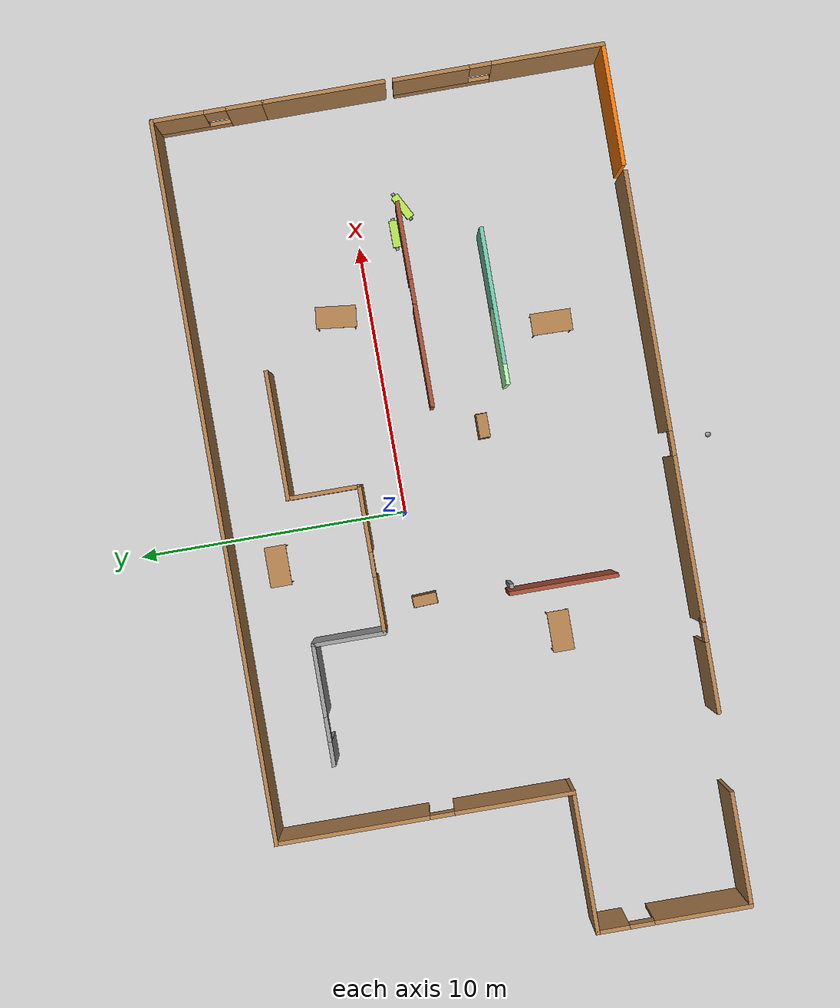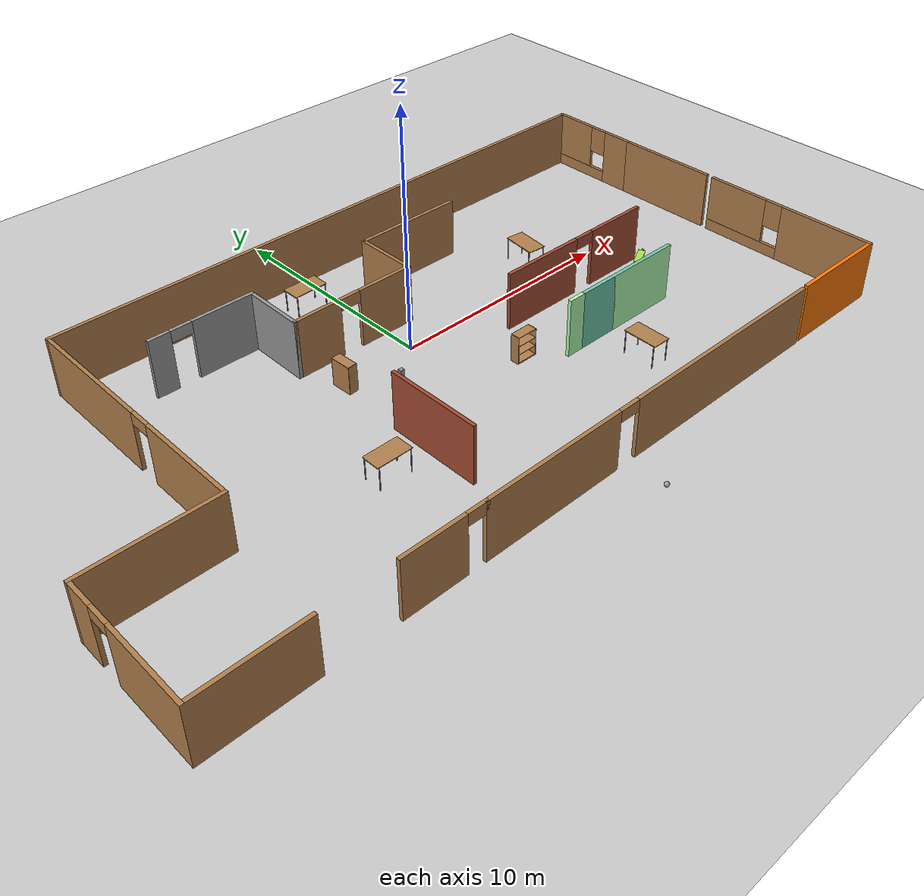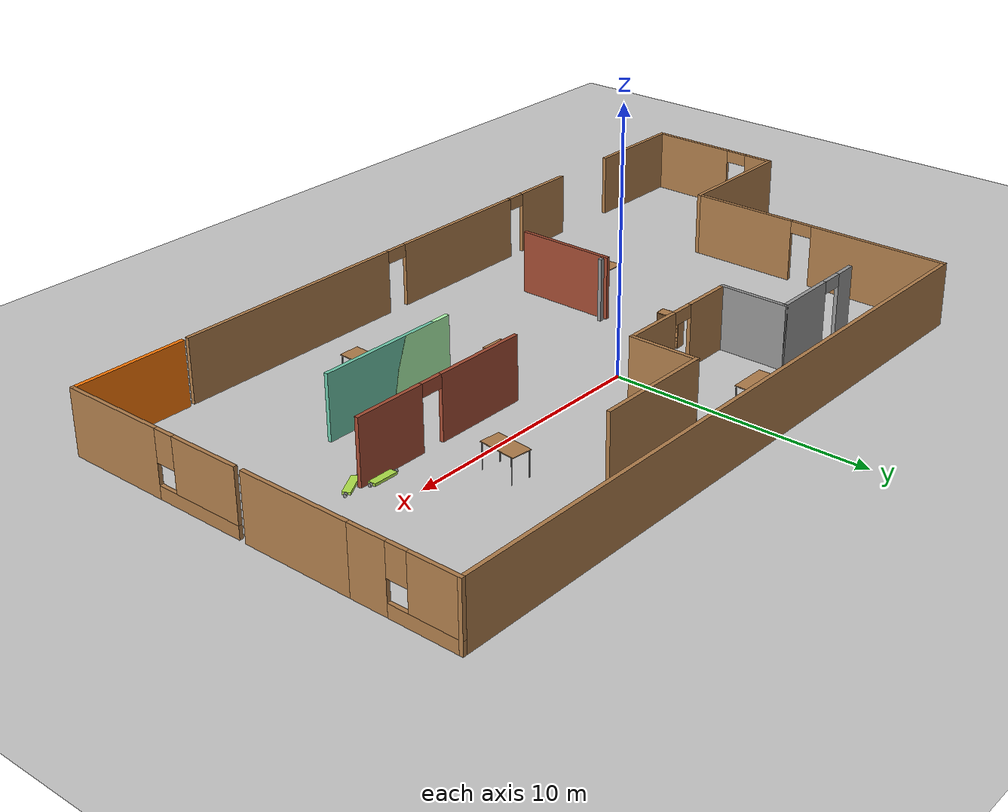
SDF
<sdf version="1.6">
 <world name="default">
  <light name="sun" type="directional">
   <pose>0 0 10 0 -0 0</pose>
   <diffuse>0.8 0.8 0.8 1</diffuse>
   <specular>0.2 0.2 0.2 1</specular>
   <attenuation>
    <range>1000</range>
    <constant>0.9</constant>
    <linear>0.01</linear>
    <quadratic>0.001</quadratic>
   </attenuation>
   <direction>-0.5 0.1 -0.9</direction>
   <spot><inner_angle>0</inner_angle><outer_angle>0</outer_angle><falloff>0</falloff></spot>
  </light>
  <model name="ground_plane">
   <static>1</static>
   <link name="link">
    <collision name="collision">
     <geometry><plane><normal>0 0 1</normal><size>100 100</size></plane></geometry>
     <surface>
      <contact><collide_bitmask>65535</collide_bitmask></contact>
      <friction><ode><mu>100</mu><mu2>50</mu2></ode></friction>
     </surface>
    </collision>
    <visual name="visual">
     <cast_shadows>0</cast_shadows>
     <geometry><plane><normal>0 0 1</normal><size>100 100</size></plane></geometry>
     <material>
      <script><uri>file://media/materials/scripts/gazebo.material</uri><name>Gazebo/Grey</name></script>
     </material>
    </visual>
   </link>
  </model>
  <gravity>0 0 -9.8</gravity>
  <magnetic_field>6e-06 2.3e-05 -4.2e-05</magnetic_field>
  <atmosphere type="adiabatic"/>
  <physics type="ode">
   <max_step_size>0.001</max_step_size>
   <real_time_factor>1</real_time_factor>
   <real_time_update_rate>1000</real_time_update_rate>
  </physics>
  <scene><ambient>0.4 0.4 0.4 1</ambient><background>0.7 0.7 0.7 1</background><shadows>1</shadows></scene>
  <spherical_coordinates>
   <surface_model>EARTH_WGS84</surface_model>
   <latitude_deg>0</latitude_deg>
   <longitude_deg>0</longitude_deg>
   <elevation>0</elevation>
   <heading_deg>0</heading_deg>
  </spherical_coordinates>
  <model name="table">
   <model name="table">
    <static>1</static>
    <link name="link">
     <collision name="surface">
      <pose>0 0 1 0 -0 0</pose>
      <geometry><box><size>1.5 0.8 0.03</size></box></geometry>
      <surface><friction><ode><mu>0.6</mu><mu2>0.6</mu2></ode></friction></surface>
     </collision>
     <visual name="visual1">
      <pose>0 0 1 0 -0 0</pose>
      <geometry><box><size>1.5 0.8 0.03</size></box></geometry>
      <material>
       <script><uri>file://media/materials/scripts/gazebo.material</uri><name>Gazebo/Wood</name></script>
      </material>
     </visual>
     <collision name="front_left_leg">
      <pose>0.68 0.38 0.5 0 -0 0</pose>
      <geometry><cylinder><radius>0.02</radius><length>1</length></cylinder></geometry>
     </collision>
     <visual name="front_left_leg">
      <pose>0.68 0.38 0.5 0 -0 0</pose>
      <geometry><cylinder><radius>0.02</radius><length>1</length></cylinder></geometry>
      <material>
       <script><uri>file://media/materials/scripts/gazebo.material</uri><name>Gazebo/Grey</name></script>
      </material>
     </visual>
     <collision name="front_right_leg">
      <pose>0.68 -0.38 0.5 0 -0 0</pose>
      <geometry><cylinder><radius>0.02</radius><length>1</length></cylinder></geometry>
     </collision>
     <visual name="front_right_leg">
      <pose>0.68 -0.38 0.5 0 -0 0</pose>
      <geometry><cylinder><radius>0.02</radius><length>1</length></cylinder></geometry>
      <material>
       <script><uri>file://media/materials/scripts/gazebo.material</uri><name>Gazebo/Grey</name></script>
      </material>
     </visual>
     <collision name="back_right_leg">
      <pose>-0.68 -0.38 0.5 0 -0 0</pose>
      <geometry><cylinder><radius>0.02</radius><length>1</length></cylinder></geometry>
     </collision>
     <visual name="back_right_leg">
      <pose>-0.68 -0.38 0.5 0 -0 0</pose>
      <geometry><cylinder><radius>0.02</radius><length>1</length></cylinder></geometry>
      <material>
       <script><uri>file://media/materials/scripts/gazebo.material</uri><name>Gazebo/Grey</name></script>
      </material>
     </visual>
     <collision name="back_left_leg">
      <pose>-0.68 0.38 0.5 0 -0 0</pose>
      <geometry><cylinder><radius>0.02</radius><length>1</length></cylinder></geometry>
     </collision>
     <visual name="back_left_leg">
      <pose>-0.68 0.38 0.5 0 -0 0</pose>
      <geometry><cylinder><radius>0.02</radius><length>1</length></cylinder></geometry>
      <material>
       <script><uri>file://media/materials/scripts/gazebo.material</uri><name>Gazebo/Grey</name></script>
      </material>
     </visual>
    </link>
   </model>
   <static>0</static>
   <pose>-1.14837 4.95371 0 0 -0 0</pose>
  </model>
  <model name="table_clone">
   <model name="table">
    <static>1</static>
    <link name="link">
     <collision name="surface">
      <pose>0 0 1 0 -0 0</pose>
      <geometry><box><size>1.5 0.8 0.03</size></box></geometry>
      <surface><friction><ode><mu>0.6</mu><mu2>0.6</mu2></ode></friction></surface>
     </collision>
     <visual name="visual1">
      <pose>0 0 1 0 -0 0</pose>
      <geometry><box><size>1.5 0.8 0.03</size></box></geometry>
      <material>
       <script><uri>file://media/materials/scripts/gazebo.material</uri><name>Gazebo/Wood</name></script>
      </material>
     </visual>
     <collision name="front_left_leg">
      <pose>0.68 0.38 0.5 0 -0 0</pose>
      <geometry><cylinder><radius>0.02</radius><length>1</length></cylinder></geometry>
     </collision>
     <visual name="front_left_leg">
      <pose>0.68 0.38 0.5 0 -0 0</pose>
      <geometry><cylinder><radius>0.02</radius><length>1</length></cylinder></geometry>
      <material>
       <script><uri>file://media/materials/scripts/gazebo.material</uri><name>Gazebo/Grey</name></script>
      </material>
     </visual>
     <collision name="front_right_leg">
      <pose>0.68 -0.38 0.5 0 -0 0</pose>
      <geometry><cylinder><radius>0.02</radius><length>1</length></cylinder></geometry>
     </collision>
     <visual name="front_right_leg">
      <pose>0.68 -0.38 0.5 0 -0 0</pose>
      <geometry><cylinder><radius>0.02</radius><length>1</length></cylinder></geometry>
      <material>
       <script><uri>file://media/materials/scripts/gazebo.material</uri><name>Gazebo/Grey</name></script>
      </material>
     </visual>
     <collision name="back_right_leg">
      <pose>-0.68 -0.38 0.5 0 -0 0</pose>
      <geometry><cylinder><radius>0.02</radius><length>1</length></cylinder></geometry>
     </collision>
     <visual name="back_right_leg">
      <pose>-0.68 -0.38 0.5 0 -0 0</pose>
      <geometry><cylinder><radius>0.02</radius><length>1</length></cylinder></geometry>
      <material>
       <script><uri>file://media/materials/scripts/gazebo.material</uri><name>Gazebo/Grey</name></script>
      </material>
     </visual>
     <collision name="back_left_leg">
      <pose>-0.68 0.38 0.5 0 -0 0</pose>
      <geometry><cylinder><radius>0.02</radius><length>1</length></cylinder></geometry>
     </collision>
     <visual name="back_left_leg">
      <pose>-0.68 0.38 0.5 0 -0 0</pose>
      <geometry><cylinder><radius>0.02</radius><length>1</length></cylinder></geometry>
      <material>
       <script><uri>file://media/materials/scripts/gazebo.material</uri><name>Gazebo/Grey</name></script>
      </material>
     </visual>
    </link>
   </model>
   <static>0</static>
   <pose>5.99818 -6.4942 0 0 -0 1.5488</pose>
  </model>
  <model name="table_clone_0">
   <model name="table">
    <static>1</static>
    <link name="link">
     <collision name="surface">
      <pose>0 0 1 0 -0 0</pose>
      <geometry><box><size>1.5 0.8 0.03</size></box></geometry>
      <surface><friction><ode><mu>0.6</mu><mu2>0.6</mu2></ode></friction></surface>
     </collision>
     <visual name="visual1">
      <pose>0 0 1 0 -0 0</pose>
      <geometry><box><size>1.5 0.8 0.03</size></box></geometry>
      <material>
       <script><uri>file://media/materials/scripts/gazebo.material</uri><name>Gazebo/Wood</name></script>
      </material>
     </visual>
     <collision name="front_left_leg">
      <pose>0.68 0.38 0.5 0 -0 0</pose>
      <geometry><cylinder><radius>0.02</radius><length>1</length></cylinder></geometry>
     </collision>
     <visual name="front_left_leg">
      <pose>0.68 0.38 0.5 0 -0 0</pose>
      <geometry><cylinder><radius>0.02</radius><length>1</length></cylinder></geometry>
      <material>
       <script><uri>file://media/materials/scripts/gazebo.material</uri><name>Gazebo/Grey</name></script>
      </material>
     </visual>
     <collision name="front_right_leg">
      <pose>0.68 -0.38 0.5 0 -0 0</pose>
      <geometry><cylinder><radius>0.02</radius><length>1</length></cylinder></geometry>
     </collision>
     <visual name="front_right_leg">
      <pose>0.68 -0.38 0.5 0 -0 0</pose>
      <geometry><cylinder><radius>0.02</radius><length>1</length></cylinder></geometry>
      <material>
       <script><uri>file://media/materials/scripts/gazebo.material</uri><name>Gazebo/Grey</name></script>
      </material>
     </visual>
     <collision name="back_right_leg">
      <pose>-0.68 -0.38 0.5 0 -0 0</pose>
      <geometry><cylinder><radius>0.02</radius><length>1</length></cylinder></geometry>
     </collision>
     <visual name="back_right_leg">
      <pose>-0.68 -0.38 0.5 0 -0 0</pose>
      <geometry><cylinder><radius>0.02</radius><length>1</length></cylinder></geometry>
      <material>
       <script><uri>file://media/materials/scripts/gazebo.material</uri><name>Gazebo/Grey</name></script>
      </material>
     </visual>
     <collision name="back_left_leg">
      <pose>-0.68 0.38 0.5 0 -0 0</pose>
      <geometry><cylinder><radius>0.02</radius><length>1</length></cylinder></geometry>
     </collision>
     <visual name="back_left_leg">
      <pose>-0.68 0.38 0.5 0 -0 0</pose>
      <geometry><cylinder><radius>0.02</radius><length>1</length></cylinder></geometry>
      <material>
       <script><uri>file://media/materials/scripts/gazebo.material</uri><name>Gazebo/Grey</name></script>
      </material>
     </visual>
    </link>
   </model>
   <static>0</static>
   <pose>-5.26231 -4.89518 0 0 -0 0</pose>
  </model>
  <model name="table_clone_clone">
   <model name="table">
    <static>1</static>
    <link name="link">
     <collision name="surface">
      <pose>0 0 1 0 -0 0</pose>
      <geometry><box><size>1.5 0.8 0.03</size></box></geometry>
      <surface><friction><ode><mu>0.6</mu><mu2>0.6</mu2></ode></friction></surface>
     </collision>
     <visual name="visual1">
      <pose>0 0 1 0 -0 0</pose>
      <geometry><box><size>1.5 0.8 0.03</size></box></geometry>
      <material>
       <script><uri>file://media/materials/scripts/gazebo.material</uri><name>Gazebo/Wood</name></script>
      </material>
     </visual>
     <collision name="front_left_leg">
      <pose>0.68 0.38 0.5 0 -0 0</pose>
      <geometry><cylinder><radius>0.02</radius><length>1</length></cylinder></geometry>
     </collision>
     <visual name="front_left_leg">
      <pose>0.68 0.38 0.5 0 -0 0</pose>
      <geometry><cylinder><radius>0.02</radius><length>1</length></cylinder></geometry>
      <material>
       <script><uri>file://media/materials/scripts/gazebo.material</uri><name>Gazebo/Grey</name></script>
      </material>
     </visual>
     <collision name="front_right_leg">
      <pose>0.68 -0.38 0.5 0 -0 0</pose>
      <geometry><cylinder><radius>0.02</radius><length>1</length></cylinder></geometry>
     </collision>
     <visual name="front_right_leg">
      <pose>0.68 -0.38 0.5 0 -0 0</pose>
      <geometry><cylinder><radius>0.02</radius><length>1</length></cylinder></geometry>
      <material>
       <script><uri>file://media/materials/scripts/gazebo.material</uri><name>Gazebo/Grey</name></script>
      </material>
     </visual>
     <collision name="back_right_leg">
      <pose>-0.68 -0.38 0.5 0 -0 0</pose>
      <geometry><cylinder><radius>0.02</radius><length>1</length></cylinder></geometry>
     </collision>
     <visual name="back_right_leg">
      <pose>-0.68 -0.38 0.5 0 -0 0</pose>
      <geometry><cylinder><radius>0.02</radius><length>1</length></cylinder></geometry>
      <material>
       <script><uri>file://media/materials/scripts/gazebo.material</uri><name>Gazebo/Grey</name></script>
      </material>
     </visual>
     <collision name="back_left_leg">
      <pose>-0.68 0.38 0.5 0 -0 0</pose>
      <geometry><cylinder><radius>0.02</radius><length>1</length></cylinder></geometry>
     </collision>
     <visual name="back_left_leg">
      <pose>-0.68 0.38 0.5 0 -0 0</pose>
      <geometry><cylinder><radius>0.02</radius><length>1</length></cylinder></geometry>
      <material>
       <script><uri>file://media/materials/scripts/gazebo.material</uri><name>Gazebo/Grey</name></script>
      </material>
     </visual>
    </link>
   </model>
   <static>0</static>
   <pose>7.53193 1.28893 0 0 -0 1.46059</pose>
  </model>
  <model name="bookshelf">
   <model name="bookshelf">
    <static>1</static>
    <link name="link">
     <inertial><mass>1</mass></inertial>
     <collision name="back">
      <pose>0 0.005 0.6 0 -0 0</pose>
      <geometry><box><size>0.9 0.01 1.2</size></box></geometry>
     </collision>
     <visual name="visual1">
      <pose>0 0.005 0.6 0 -0 0</pose>
      <geometry><box><size>0.9 0.01 1.2</size></box></geometry>
      <material>
       <script><uri>file://media/materials/scripts/gazebo.material</uri><name>Gazebo/Wood</name></script>
      </material>
     </visual>
     <collision name="left_side">
      <pose>0.45 -0.195 0.6 0 -0 0</pose>
      <geometry><box><size>0.02 0.4 1.2</size></box></geometry>
     </collision>
     <visual name="visual2">
      <pose>0.45 -0.195 0.6 0 -0 0</pose>
      <geometry><box><size>0.02 0.4 1.2</size></box></geometry>
      <material>
       <script><uri>file://media/materials/scripts/gazebo.material</uri><name>Gazebo/Wood</name></script>
      </material>
     </visual>
     <collision name="right_side">
      <pose>-0.45 -0.195 0.6 0 -0 0</pose>
      <geometry><box><size>0.02 0.4 1.2</size></box></geometry>
     </collision>
     <visual name="visual3">
      <pose>-0.45 -0.195 0.6 0 -0 0</pose>
      <geometry><box><size>0.02 0.4 1.2</size></box></geometry>
      <material>
       <script><uri>file://media/materials/scripts/gazebo.material</uri><name>Gazebo/Wood</name></script>
      </material>
     </visual>
     <collision name="bottom">
      <pose>0 -0.195 0.03 0 -0 0</pose>
      <geometry><box><size>0.88 0.4 0.06</size></box></geometry>
     </collision>
     <visual name="visual4">
      <pose>0 -0.195 0.03 0 -0 0</pose>
      <geometry><box><size>0.88 0.4 0.06</size></box></geometry>
      <material>
       <script><uri>file://media/materials/scripts/gazebo.material</uri><name>Gazebo/Wood</name></script>
      </material>
     </visual>
     <collision name="top">
      <pose>0 -0.195 1.19 0 -0 0</pose>
      <geometry><box><size>0.88 0.4 0.02</size></box></geometry>
     </collision>
     <visual name="visual5">
      <pose>0 -0.195 1.19 0 -0 0</pose>
      <geometry><box><size>0.88 0.4 0.02</size></box></geometry>
      <material>
       <script><uri>file://media/materials/scripts/gazebo.material</uri><name>Gazebo/Wood</name></script>
      </material>
     </visual>
     <collision name="low_shelf">
      <pose>0 -0.195 0.43 0 -0 0</pose>
      <geometry><box><size>0.88 0.4 0.02</size></box></geometry>
     </collision>
     <visual name="visual6">
      <pose>0 -0.195 0.43 0 -0 0</pose>
      <geometry><box><size>0.88 0.4 0.02</size></box></geometry>
      <material>
       <script><uri>file://media/materials/scripts/gazebo.material</uri><name>Gazebo/Wood</name></script>
      </material>
     </visual>
     <collision name="high_shelf">
      <pose>0 -0.195 0.8 0 -0 0</pose>
      <geometry><box><size>0.88 0.4 0.02</size></box></geometry>
     </collision>
     <visual name="visual7">
      <pose>0 -0.195 0.8 0 -0 0</pose>
      <geometry><box><size>0.88 0.4 0.02</size></box></geometry>
      <material>
       <script><uri>file://media/materials/scripts/gazebo.material</uri><name>Gazebo/Wood</name></script>
      </material>
     </visual>
    </link>
    <pose>-4e-06 4e-06 0 0 -0 0</pose>
   </model>
   <static>0</static>
   <pose>2.66139 -3.16627 0 0 -0 0</pose>
  </model>
  <model name="bookshelf_clone">
   <model name="bookshelf">
    <static>1</static>
    <link name="link">
     <inertial><mass>1</mass></inertial>
     <collision name="back">
      <pose>0 0.005 0.6 0 -0 0</pose>
      <geometry><box><size>0.9 0.01 1.2</size></box></geometry>
     </collision>
     <visual name="visual1">
      <pose>0 0.005 0.6 0 -0 0</pose>
      <geometry><box><size>0.9 0.01 1.2</size></box></geometry>
      <material>
       <script><uri>file://media/materials/scripts/gazebo.material</uri><name>Gazebo/Wood</name></script>
      </material>
     </visual>
     <collision name="left_side">
      <pose>0.45 -0.195 0.6 0 -0 0</pose>
      <geometry><box><size>0.02 0.4 1.2</size></box></geometry>
     </collision>
     <visual name="visual2">
      <pose>0.45 -0.195 0.6 0 -0 0</pose>
      <geometry><box><size>0.02 0.4 1.2</size></box></geometry>
      <material>
       <script><uri>file://media/materials/scripts/gazebo.material</uri><name>Gazebo/Wood</name></script>
      </material>
     </visual>
     <collision name="right_side">
      <pose>-0.45 -0.195 0.6 0 -0 0</pose>
      <geometry><box><size>0.02 0.4 1.2</size></box></geometry>
     </collision>
     <visual name="visual3">
      <pose>-0.45 -0.195 0.6 0 -0 0</pose>
      <geometry><box><size>0.02 0.4 1.2</size></box></geometry>
      <material>
       <script><uri>file://media/materials/scripts/gazebo.material</uri><name>Gazebo/Wood</name></script>
      </material>
     </visual>
     <collision name="bottom">
      <pose>0 -0.195 0.03 0 -0 0</pose>
      <geometry><box><size>0.88 0.4 0.06</size></box></geometry>
     </collision>
     <visual name="visual4">
      <pose>0 -0.195 0.03 0 -0 0</pose>
      <geometry><box><size>0.88 0.4 0.06</size></box></geometry>
      <material>
       <script><uri>file://media/materials/scripts/gazebo.material</uri><name>Gazebo/Wood</name></script>
      </material>
     </visual>
     <collision name="top">
      <pose>0 -0.195 1.19 0 -0 0</pose>
      <geometry><box><size>0.88 0.4 0.02</size></box></geometry>
     </collision>
     <visual name="visual5">
      <pose>0 -0.195 1.19 0 -0 0</pose>
      <geometry><box><size>0.88 0.4 0.02</size></box></geometry>
      <material>
       <script><uri>file://media/materials/scripts/gazebo.material</uri><name>Gazebo/Wood</name></script>
      </material>
     </visual>
     <collision name="low_shelf">
      <pose>0 -0.195 0.43 0 -0 0</pose>
      <geometry><box><size>0.88 0.4 0.02</size></box></geometry>
     </collision>
     <visual name="visual6">
      <pose>0 -0.195 0.43 0 -0 0</pose>
      <geometry><box><size>0.88 0.4 0.02</size></box></geometry>
      <material>
       <script><uri>file://media/materials/scripts/gazebo.material</uri><name>Gazebo/Wood</name></script>
      </material>
     </visual>
     <collision name="high_shelf">
      <pose>0 -0.195 0.8 0 -0 0</pose>
      <geometry><box><size>0.88 0.4 0.02</size></box></geometry>
     </collision>
     <visual name="visual7">
      <pose>0 -0.195 0.8 0 -0 0</pose>
      <geometry><box><size>0.88 0.4 0.02</size></box></geometry>
      <material>
       <script><uri>file://media/materials/scripts/gazebo.material</uri><name>Gazebo/Wood</name></script>
      </material>
     </visual>
    </link>
    <pose>-4e-06 4e-06 0 0 -0 0</pose>
   </model>
   <static>0</static>
   <pose>-3.47779 -0.174747 0 0 -0 1.61922</pose>
  </model>
  <model name="floorplan">
   <link name="Wall_1">
    <pose>-2.93248 -1.67538 0 0 -0 0</pose>
    <visual name="Wall_1_Visual">
     <pose>0 0 1.25 0 -0 0</pose>
     <geometry><box><size>0.16 0.15 2.5</size></box></geometry>
     <material>
      <script><uri>file://media/materials/scripts/gazebo.material</uri><name>Gazebo/Grey</name></script>
      <ambient>0 0 0 1</ambient>
      <shader type="pixel"/>
     </material>
     <meta><layer>0</layer></meta>
    </visual>
    <collision name="Wall_1_Collision">
     <pose>0 0 1.25 0 -0 0</pose>
     <geometry><box><size>0.16 0.15 2.5</size></box></geometry>
     <surface>
      <friction>
       <ode><mu>1</mu><mu2>1</mu2><fdir1>0 0 0</fdir1><slip1>0</slip1><slip2>0</slip2></ode>
       <torsional>
        <coefficient>1</coefficient>
        <patch_radius>0</patch_radius>
        <surface_radius>0</surface_radius>
        <use_patch_radius>1</use_patch_radius>
        <ode><slip>0</slip></ode>
       </torsional>
      </friction>
      <bounce><restitution_coefficient>0</restitution_coefficient><threshold>1e+06</threshold></bounce>
      <contact>
       <collide_without_contact>0</collide_without_contact>
       <collide_without_contact_bitmask>1</collide_without_contact_bitmask>
       <collide_bitmask>1</collide_bitmask>
       <ode>
        <soft_cfm>0</soft_cfm>
        <soft_erp>0.2</soft_erp>
        <kp>1e+13</kp>
        <kd>1</kd>
        <max_vel>0.01</max_vel>
        <min_depth>0</min_depth>
       </ode>
       <bullet>
        <split_impulse>1</split_impulse>
        <split_impulse_penetration_threshold>-0.01</split_impulse_penetration_threshold>
        <soft_cfm>0</soft_cfm>
        <soft_erp>0.2</soft_erp>
        <kp>1e+13</kp>
        <kd>1</kd>
       </bullet>
      </contact>
     </surface>
    </collision>
   </link>
   <link name="Wall_10">
    <pose>15.7094 -4.42431 0 0 -0 1.5708</pose>
    <visual name="Wall_10_Visual_0">
     <pose>-1.80178 0 1.25 0 -0 0</pose>
     <geometry><box><size>4.14643 0.15 2.5</size></box></geometry>
     <material>
      <script><uri>file://media/materials/scripts/gazebo.material</uri><name>Gazebo/Wood</name></script>
      <ambient>0.996078 0.47451 0.0196078 1</ambient>
      <shader type="pixel"/>
     </material>
     <meta><layer>0</layer></meta>
    </visual>
    <visual name="Wall_10_Visual_1">
     <pose>2.07322 0 0.25 0 -0 0</pose>
     <geometry><box><size>3.60357 0.15 0.5</size></box></geometry>
     <material>
      <script><uri>file://media/materials/scripts/gazebo.material</uri><name>Gazebo/Wood</name></script>
      <ambient>0.996078 0.47451 0.0196078 1</ambient>
      <shader type="pixel"/>
     </material>
     <meta><layer>0</layer></meta>
    </visual>
    <visual name="Wall_10_Visual_2">
     <pose>2.47322 0 1.5 0 -0 0</pose>
     <geometry><box><size>2.80357 0.15 2</size></box></geometry>
     <material>
      <script><uri>file://media/materials/scripts/gazebo.material</uri><name>Gazebo/Wood</name></script>
      <ambient>0.996078 0.47451 0.0196078 1</ambient>
      <shader type="pixel"/>
     </material>
     <meta><layer>0</layer></meta>
    </visual>
    <visual name="Wall_10_Visual_3">
     <pose>0.671434 0 1.9 0 -0 0</pose>
     <geometry><box><size>0.8 0.15 1.2</size></box></geometry>
     <material>
      <script><uri>file://media/materials/scripts/gazebo.material</uri><name>Gazebo/Wood</name></script>
      <ambient>0.996078 0.47451 0.0196078 1</ambient>
      <shader type="pixel"/>
     </material>
     <meta><layer>0</layer></meta>
    </visual>
    <collision name="Wall_10_Collision_0">
     <pose>-1.80178 0 1.25 0 -0 0</pose>
     <geometry><box><size>4.14643 0.15 2.5</size></box></geometry>
     <surface>
      <friction>
       <ode><mu>1</mu><mu2>1</mu2><fdir1>0 0 0</fdir1><slip1>0</slip1><slip2>0</slip2></ode>
       <torsional>
        <coefficient>1</coefficient>
        <patch_radius>0</patch_radius>
        <surface_radius>0</surface_radius>
        <use_patch_radius>1</use_patch_radius>
        <ode><slip>0</slip></ode>
       </torsional>
      </friction>
      <bounce><restitution_coefficient>0</restitution_coefficient><threshold>1e+06</threshold></bounce>
      <contact>
       <collide_without_contact>0</collide_without_contact>
       <collide_without_contact_bitmask>1</collide_without_contact_bitmask>
       <collide_bitmask>1</collide_bitmask>
       <ode>
        <soft_cfm>0</soft_cfm>
        <soft_erp>0.2</soft_erp>
        <kp>1e+13</kp>
        <kd>1</kd>
        <max_vel>0.01</max_vel>
        <min_depth>0</min_depth>
       </ode>
       <bullet>
        <split_impulse>1</split_impulse>
        <split_impulse_penetration_threshold>-0.01</split_impulse_penetration_threshold>
        <soft_cfm>0</soft_cfm>
        <soft_erp>0.2</soft_erp>
        <kp>1e+13</kp>
        <kd>1</kd>
       </bullet>
      </contact>
     </surface>
    </collision>
    <collision name="Wall_10_Collision_1">
     <pose>2.07322 0 0.25 0 -0 0</pose>
     <geometry><box><size>3.60357 0.15 0.5</size></box></geometry>
     <surface>
      <friction>
       <ode><mu>1</mu><mu2>1</mu2><fdir1>0 0 0</fdir1><slip1>0</slip1><slip2>0</slip2></ode>
       <torsional>
        <coefficient>1</coefficient>
        <patch_radius>0</patch_radius>
        <surface_radius>0</surface_radius>
        <use_patch_radius>1</use_patch_radius>
        <ode><slip>0</slip></ode>
       </torsional>
      </friction>
      <bounce><restitution_coefficient>0</restitution_coefficient><threshold>1e+06</threshold></bounce>
      <contact>
       <collide_without_contact>0</collide_without_contact>
       <collide_without_contact_bitmask>1</collide_without_contact_bitmask>
       <collide_bitmask>1</collide_bitmask>
       <ode>
        <soft_cfm>0</soft_cfm>
        <soft_erp>0.2</soft_erp>
        <kp>1e+13</kp>
        <kd>1</kd>
        <max_vel>0.01</max_vel>
        <min_depth>0</min_depth>
       </ode>
       <bullet>
        <split_impulse>1</split_impulse>
        <split_impulse_penetration_threshold>-0.01</split_impulse_penetration_threshold>
        <soft_cfm>0</soft_cfm>
        <soft_erp>0.2</soft_erp>
        <kp>1e+13</kp>
        <kd>1</kd>
       </bullet>
      </contact>
     </surface>
    </collision>
    <collision name="Wall_10_Collision_2">
     <pose>2.47322 0 1.5 0 -0 0</pose>
     <geometry><box><size>2.80357 0.15 2</size></box></geometry>
     <surface>
      <friction>
       <ode><mu>1</mu><mu2>1</mu2><fdir1>0 0 0</fdir1><slip1>0</slip1><slip2>0</slip2></ode>
       <torsional>
        <coefficient>1</coefficient>
        <patch_radius>0</patch_radius>
        <surface_radius>0</surface_radius>
        <use_patch_radius>1</use_patch_radius>
        <ode><slip>0</slip></ode>
       </torsional>
      </friction>
      <bounce><restitution_coefficient>0</restitution_coefficient><threshold>1e+06</threshold></bounce>
      <contact>
       <collide_without_contact>0</collide_without_contact>
       <collide_without_contact_bitmask>1</collide_without_contact_bitmask>
       <collide_bitmask>1</collide_bitmask>
       <ode>
        <soft_cfm>0</soft_cfm>
        <soft_erp>0.2</soft_erp>
        <kp>1e+13</kp>
        <kd>1</kd>
        <max_vel>0.01</max_vel>
        <min_depth>0</min_depth>
       </ode>
       <bullet>
        <split_impulse>1</split_impulse>
        <split_impulse_penetration_threshold>-0.01</split_impulse_penetration_threshold>
        <soft_cfm>0</soft_cfm>
        <soft_erp>0.2</soft_erp>
        <kp>1e+13</kp>
        <kd>1</kd>
       </bullet>
      </contact>
     </surface>
    </collision>
    <collision name="Wall_10_Collision_3">
     <pose>0.671434 0 1.9 0 -0 0</pose>
     <geometry><box><size>0.8 0.15 1.2</size></box></geometry>
     <surface>
      <friction>
       <ode><mu>1</mu><mu2>1</mu2><fdir1>0 0 0</fdir1><slip1>0</slip1><slip2>0</slip2></ode>
       <torsional>
        <coefficient>1</coefficient>
        <patch_radius>0</patch_radius>
        <surface_radius>0</surface_radius>
        <use_patch_radius>1</use_patch_radius>
        <ode><slip>0</slip></ode>
       </torsional>
      </friction>
      <bounce><restitution_coefficient>0</restitution_coefficient><threshold>1e+06</threshold></bounce>
      <contact>
       <collide_without_contact>0</collide_without_contact>
       <collide_without_contact_bitmask>1</collide_without_contact_bitmask>
       <collide_bitmask>1</collide_bitmask>
       <ode>
        <soft_cfm>0</soft_cfm>
        <soft_erp>0.2</soft_erp>
        <kp>1e+13</kp>
        <kd>1</kd>
        <max_vel>0.01</max_vel>
        <min_depth>0</min_depth>
       </ode>
       <bullet>
        <split_impulse>1</split_impulse>
        <split_impulse_penetration_threshold>-0.01</split_impulse_penetration_threshold>
        <soft_cfm>0</soft_cfm>
        <soft_erp>0.2</soft_erp>
        <kp>1e+13</kp>
        <kd>1</kd>
       </bullet>
      </contact>
     </surface>
    </collision>
   </link>
   <link name="Wall_16">
    <pose>15.725 1.96893 0 0 -0 1.5708</pose>
    <visual name="Wall_16_Visual">
     <pose>0 0 1.25 0 -0 0</pose>
     <geometry><box><size>4.5 0.15 2.5</size></box></geometry>
     <material>
      <script><uri>file://media/materials/scripts/gazebo.material</uri><name>Gazebo/Wood</name></script>
      <ambient>0.996078 0.47451 0.0196078 1</ambient>
      <shader type="pixel"/>
     </material>
     <meta><layer>0</layer></meta>
    </visual>
    <collision name="Wall_16_Collision">
     <pose>0 0 1.25 0 -0 0</pose>
     <geometry><box><size>4.5 0.15 2.5</size></box></geometry>
     <surface>
      <friction>
       <ode><mu>1</mu><mu2>1</mu2><fdir1>0 0 0</fdir1><slip1>0</slip1><slip2>0</slip2></ode>
       <torsional>
        <coefficient>1</coefficient>
        <patch_radius>0</patch_radius>
        <surface_radius>0</surface_radius>
        <use_patch_radius>1</use_patch_radius>
        <ode><slip>0</slip></ode>
       </torsional>
      </friction>
      <bounce><restitution_coefficient>0</restitution_coefficient><threshold>1e+06</threshold></bounce>
      <contact>
       <collide_without_contact>0</collide_without_contact>
       <collide_without_contact_bitmask>1</collide_without_contact_bitmask>
       <collide_bitmask>1</collide_bitmask>
       <ode>
        <soft_cfm>0</soft_cfm>
        <soft_erp>0.2</soft_erp>
        <kp>1e+13</kp>
        <kd>1</kd>
        <max_vel>0.01</max_vel>
        <min_depth>0</min_depth>
       </ode>
       <bullet>
        <split_impulse>1</split_impulse>
        <split_impulse_penetration_threshold>-0.01</split_impulse_penetration_threshold>
        <soft_cfm>0</soft_cfm>
        <soft_erp>0.2</soft_erp>
        <kp>1e+13</kp>
        <kd>1</kd>
       </bullet>
      </contact>
     </surface>
    </collision>
   </link>
   <link name="Wall_20">
    <pose>15.725 6.19393 0 0 -0 1.5708</pose>
    <visual name="Wall_20_Visual_0">
     <pose>-1.39393 0 1.25 0 -0 0</pose>
     <geometry><box><size>1.46215 0.15 2.5</size></box></geometry>
     <material>
      <script><uri>file://media/materials/scripts/gazebo.material</uri><name>Gazebo/Wood</name></script>
      <ambient>1 1 1 1</ambient>
      <shader type="pixel"/>
     </material>
     <meta><layer>0</layer></meta>
    </visual>
    <visual name="Wall_20_Visual_1">
     <pose>0.731073 0 0.25 0 -0 0</pose>
     <geometry><box><size>2.78785 0.15 0.5</size></box></geometry>
     <material>
      <script><uri>file://media/materials/scripts/gazebo.material</uri><name>Gazebo/Wood</name></script>
      <ambient>1 1 1 1</ambient>
      <shader type="pixel"/>
     </material>
     <meta><layer>0</layer></meta>
    </visual>
    <visual name="Wall_20_Visual_2">
     <pose>1.13107 0 1.5 0 -0 0</pose>
     <geometry><box><size>1.98785 0.15 2</size></box></geometry>
     <material>
      <script><uri>file://media/materials/scripts/gazebo.material</uri><name>Gazebo/Wood</name></script>
      <ambient>1 1 1 1</ambient>
      <shader type="pixel"/>
     </material>
     <meta><layer>0</layer></meta>
    </visual>
    <visual name="Wall_20_Visual_3">
     <pose>-0.262854 0 1.9 0 -0 0</pose>
     <geometry><box><size>0.8 0.15 1.2</size></box></geometry>
     <material>
      <script><uri>file://media/materials/scripts/gazebo.material</uri><name>Gazebo/Wood</name></script>
      <ambient>1 1 1 1</ambient>
      <shader type="pixel"/>
     </material>
     <meta><layer>0</layer></meta>
    </visual>
    <collision name="Wall_20_Collision_0">
     <pose>-1.39393 0 1.25 0 -0 0</pose>
     <geometry><box><size>1.46215 0.15 2.5</size></box></geometry>
     <surface>
      <friction>
       <ode><mu>1</mu><mu2>1</mu2><fdir1>0 0 0</fdir1><slip1>0</slip1><slip2>0</slip2></ode>
       <torsional>
        <coefficient>1</coefficient>
        <patch_radius>0</patch_radius>
        <surface_radius>0</surface_radius>
        <use_patch_radius>1</use_patch_radius>
        <ode><slip>0</slip></ode>
       </torsional>
      </friction>
      <bounce><restitution_coefficient>0</restitution_coefficient><threshold>1e+06</threshold></bounce>
      <contact>
       <collide_without_contact>0</collide_without_contact>
       <collide_without_contact_bitmask>1</collide_without_contact_bitmask>
       <collide_bitmask>1</collide_bitmask>
       <ode>
        <soft_cfm>0</soft_cfm>
        <soft_erp>0.2</soft_erp>
        <kp>1e+13</kp>
        <kd>1</kd>
        <max_vel>0.01</max_vel>
        <min_depth>0</min_depth>
       </ode>
       <bullet>
        <split_impulse>1</split_impulse>
        <split_impulse_penetration_threshold>-0.01</split_impulse_penetration_threshold>
        <soft_cfm>0</soft_cfm>
        <soft_erp>0.2</soft_erp>
        <kp>1e+13</kp>
        <kd>1</kd>
       </bullet>
      </contact>
     </surface>
    </collision>
    <collision name="Wall_20_Collision_1">
     <pose>0.731073 0 0.25 0 -0 0</pose>
     <geometry><box><size>2.78785 0.15 0.5</size></box></geometry>
     <surface>
      <friction>
       <ode><mu>1</mu><mu2>1</mu2><fdir1>0 0 0</fdir1><slip1>0</slip1><slip2>0</slip2></ode>
       <torsional>
        <coefficient>1</coefficient>
        <patch_radius>0</patch_radius>
        <surface_radius>0</surface_radius>
        <use_patch_radius>1</use_patch_radius>
        <ode><slip>0</slip></ode>
       </torsional>
      </friction>
      <bounce><restitution_coefficient>0</restitution_coefficient><threshold>1e+06</threshold></bounce>
      <contact>
       <collide_without_contact>0</collide_without_contact>
       <collide_without_contact_bitmask>1</collide_without_contact_bitmask>
       <collide_bitmask>1</collide_bitmask>
       <ode>
        <soft_cfm>0</soft_cfm>
        <soft_erp>0.2</soft_erp>
        <kp>1e+13</kp>
        <kd>1</kd>
        <max_vel>0.01</max_vel>
        <min_depth>0</min_depth>
       </ode>
       <bullet>
        <split_impulse>1</split_impulse>
        <split_impulse_penetration_threshold>-0.01</split_impulse_penetration_threshold>
        <soft_cfm>0</soft_cfm>
        <soft_erp>0.2</soft_erp>
        <kp>1e+13</kp>
        <kd>1</kd>
       </bullet>
      </contact>
     </surface>
    </collision>
    <collision name="Wall_20_Collision_2">
     <pose>1.13107 0 1.5 0 -0 0</pose>
     <geometry><box><size>1.98785 0.15 2</size></box></geometry>
     <surface>
      <friction>
       <ode><mu>1</mu><mu2>1</mu2><fdir1>0 0 0</fdir1><slip1>0</slip1><slip2>0</slip2></ode>
       <torsional>
        <coefficient>1</coefficient>
        <patch_radius>0</patch_radius>
        <surface_radius>0</surface_radius>
        <use_patch_radius>1</use_patch_radius>
        <ode><slip>0</slip></ode>
       </torsional>
      </friction>
      <bounce><restitution_coefficient>0</restitution_coefficient><threshold>1e+06</threshold></bounce>
      <contact>
       <collide_without_contact>0</collide_without_contact>
       <collide_without_contact_bitmask>1</collide_without_contact_bitmask>
       <collide_bitmask>1</collide_bitmask>
       <ode>
        <soft_cfm>0</soft_cfm>
        <soft_erp>0.2</soft_erp>
        <kp>1e+13</kp>
        <kd>1</kd>
        <max_vel>0.01</max_vel>
        <min_depth>0</min_depth>
       </ode>
       <bullet>
        <split_impulse>1</split_impulse>
        <split_impulse_penetration_threshold>-0.01</split_impulse_penetration_threshold>
        <soft_cfm>0</soft_cfm>
        <soft_erp>0.2</soft_erp>
        <kp>1e+13</kp>
        <kd>1</kd>
       </bullet>
      </contact>
     </surface>
    </collision>
    <collision name="Wall_20_Collision_3">
     <pose>-0.262854 0 1.9 0 -0 0</pose>
     <geometry><box><size>0.8 0.15 1.2</size></box></geometry>
     <surface>
      <friction>
       <ode><mu>1</mu><mu2>1</mu2><fdir1>0 0 0</fdir1><slip1>0</slip1><slip2>0</slip2></ode>
       <torsional>
        <coefficient>1</coefficient>
        <patch_radius>0</patch_radius>
        <surface_radius>0</surface_radius>
        <use_patch_radius>1</use_patch_radius>
        <ode><slip>0</slip></ode>
       </torsional>
      </friction>
      <bounce><restitution_coefficient>0</restitution_coefficient><threshold>1e+06</threshold></bounce>
      <contact>
       <collide_without_contact>0</collide_without_contact>
       <collide_without_contact_bitmask>1</collide_without_contact_bitmask>
       <collide_bitmask>1</collide_bitmask>
       <ode>
        <soft_cfm>0</soft_cfm>
        <soft_erp>0.2</soft_erp>
        <kp>1e+13</kp>
        <kd>1</kd>
        <max_vel>0.01</max_vel>
        <min_depth>0</min_depth>
       </ode>
       <bullet>
        <split_impulse>1</split_impulse>
        <split_impulse_penetration_threshold>-0.01</split_impulse_penetration_threshold>
        <soft_cfm>0</soft_cfm>
        <soft_erp>0.2</soft_erp>
        <kp>1e+13</kp>
        <kd>1</kd>
       </bullet>
      </contact>
     </surface>
    </collision>
   </link>
   <link name="Wall_21">
    <pose>2.55 8.24393 0 0 -0 3.14159</pose>
    <visual name="Wall_21_Visual">
     <pose>0 0 1.25 0 -0 0</pose>
     <geometry><box><size>26.5 0.15 2.5</size></box></geometry>
     <material>
      <script><uri>file://media/materials/scripts/gazebo.material</uri><name>Gazebo/Wood</name></script>
      <ambient>0.435294 0.796078 0.67451 1</ambient>
      <shader type="pixel"/>
     </material>
     <meta><layer>0</layer></meta>
    </visual>
    <collision name="Wall_21_Collision">
     <pose>0 0 1.25 0 -0 0</pose>
     <geometry><box><size>26.5 0.15 2.5</size></box></geometry>
     <surface>
      <friction>
       <ode><mu>1</mu><mu2>1</mu2><fdir1>0 0 0</fdir1><slip1>0</slip1><slip2>0</slip2></ode>
       <torsional>
        <coefficient>1</coefficient>
        <patch_radius>0</patch_radius>
        <surface_radius>0</surface_radius>
        <use_patch_radius>1</use_patch_radius>
        <ode><slip>0</slip></ode>
       </torsional>
      </friction>
      <bounce><restitution_coefficient>0</restitution_coefficient><threshold>1e+06</threshold></bounce>
      <contact>
       <collide_without_contact>0</collide_without_contact>
       <collide_without_contact_bitmask>1</collide_without_contact_bitmask>
       <collide_bitmask>1</collide_bitmask>
       <ode>
        <soft_cfm>0</soft_cfm>
        <soft_erp>0.2</soft_erp>
        <kp>1e+13</kp>
        <kd>1</kd>
        <max_vel>0.01</max_vel>
        <min_depth>0</min_depth>
       </ode>
       <bullet>
        <split_impulse>1</split_impulse>
        <split_impulse_penetration_threshold>-0.01</split_impulse_penetration_threshold>
        <soft_cfm>0</soft_cfm>
        <soft_erp>0.2</soft_erp>
        <kp>1e+13</kp>
        <kd>1</kd>
       </bullet>
      </contact>
     </surface>
    </collision>
   </link>
   <link name="Wall_22">
    <pose>-10.625 2.81893 0 0 0 -1.5708</pose>
    <visual name="Wall_22_Visual_0">
     <pose>-2.65849 0 1.25 0 -0 0</pose>
     <geometry><box><size>5.68303 0.15 2.5</size></box></geometry>
     <material>
      <script><uri>file://media/materials/scripts/gazebo.material</uri><name>Gazebo/Wood</name></script>
      <ambient>0.996078 0.47451 0.0196078 1</ambient>
      <shader type="pixel"/>
     </material>
     <meta><layer>0</layer></meta>
    </visual>
    <visual name="Wall_22_Visual_1">
     <pose>3.29151 0 1.25 0 -0 0</pose>
     <geometry><box><size>4.41697 0.15 2.5</size></box></geometry>
     <material>
      <script><uri>file://media/materials/scripts/gazebo.material</uri><name>Gazebo/Wood</name></script>
      <ambient>0.996078 0.47451 0.0196078 1</ambient>
      <shader type="pixel"/>
     </material>
     <meta><layer>0</layer></meta>
    </visual>
    <visual name="Wall_22_Visual_2">
     <pose>0.633029 0 2.25 0 -0 0</pose>
     <geometry><box><size>0.9 0.15 0.5</size></box></geometry>
     <material>
      <script><uri>file://media/materials/scripts/gazebo.material</uri><name>Gazebo/Wood</name></script>
      <ambient>0.996078 0.47451 0.0196078 1</ambient>
      <shader type="pixel"/>
     </material>
     <meta><layer>0</layer></meta>
    </visual>
    <collision name="Wall_22_Collision_0">
     <pose>-2.65849 0 1.25 0 -0 0</pose>
     <geometry><box><size>5.68303 0.15 2.5</size></box></geometry>
     <surface>
      <friction>
       <ode><mu>1</mu><mu2>1</mu2><fdir1>0 0 0</fdir1><slip1>0</slip1><slip2>0</slip2></ode>
       <torsional>
        <coefficient>1</coefficient>
        <patch_radius>0</patch_radius>
        <surface_radius>0</surface_radius>
        <use_patch_radius>1</use_patch_radius>
        <ode><slip>0</slip></ode>
       </torsional>
      </friction>
      <bounce><restitution_coefficient>0</restitution_coefficient><threshold>1e+06</threshold></bounce>
      <contact>
       <collide_without_contact>0</collide_without_contact>
       <collide_without_contact_bitmask>1</collide_without_contact_bitmask>
       <collide_bitmask>1</collide_bitmask>
       <ode>
        <soft_cfm>0</soft_cfm>
        <soft_erp>0.2</soft_erp>
        <kp>1e+13</kp>
        <kd>1</kd>
        <max_vel>0.01</max_vel>
        <min_depth>0</min_depth>
       </ode>
       <bullet>
        <split_impulse>1</split_impulse>
        <split_impulse_penetration_threshold>-0.01</split_impulse_penetration_threshold>
        <soft_cfm>0</soft_cfm>
        <soft_erp>0.2</soft_erp>
        <kp>1e+13</kp>
        <kd>1</kd>
       </bullet>
      </contact>
     </surface>
    </collision>
    <collision name="Wall_22_Collision_1">
     <pose>3.29151 0 1.25 0 -0 0</pose>
     <geometry><box><size>4.41697 0.15 2.5</size></box></geometry>
     <surface>
      <friction>
       <ode><mu>1</mu><mu2>1</mu2><fdir1>0 0 0</fdir1><slip1>0</slip1><slip2>0</slip2></ode>
       <torsional>
        <coefficient>1</coefficient>
        <patch_radius>0</patch_radius>
        <surface_radius>0</surface_radius>
        <use_patch_radius>1</use_patch_radius>
        <ode><slip>0</slip></ode>
       </torsional>
      </friction>
      <bounce><restitution_coefficient>0</restitution_coefficient><threshold>1e+06</threshold></bounce>
      <contact>
       <collide_without_contact>0</collide_without_contact>
       <collide_without_contact_bitmask>1</collide_without_contact_bitmask>
       <collide_bitmask>1</collide_bitmask>
       <ode>
        <soft_cfm>0</soft_cfm>
        <soft_erp>0.2</soft_erp>
        <kp>1e+13</kp>
        <kd>1</kd>
        <max_vel>0.01</max_vel>
        <min_depth>0</min_depth>
       </ode>
       <bullet>
        <split_impulse>1</split_impulse>
        <split_impulse_penetration_threshold>-0.01</split_impulse_penetration_threshold>
        <soft_cfm>0</soft_cfm>
        <soft_erp>0.2</soft_erp>
        <kp>1e+13</kp>
        <kd>1</kd>
       </bullet>
      </contact>
     </surface>
    </collision>
    <collision name="Wall_22_Collision_2">
     <pose>0.633029 0 2.25 0 -0 0</pose>
     <geometry><box><size>0.9 0.15 0.5</size></box></geometry>
     <surface>
      <friction>
       <ode><mu>1</mu><mu2>1</mu2><fdir1>0 0 0</fdir1><slip1>0</slip1><slip2>0</slip2></ode>
       <torsional>
        <coefficient>1</coefficient>
        <patch_radius>0</patch_radius>
        <surface_radius>0</surface_radius>
        <use_patch_radius>1</use_patch_radius>
        <ode><slip>0</slip></ode>
       </torsional>
      </friction>
      <bounce><restitution_coefficient>0</restitution_coefficient><threshold>1e+06</threshold></bounce>
      <contact>
       <collide_without_contact>0</collide_without_contact>
       <collide_without_contact_bitmask>1</collide_without_contact_bitmask>
       <collide_bitmask>1</collide_bitmask>
       <ode>
        <soft_cfm>0</soft_cfm>
        <soft_erp>0.2</soft_erp>
        <kp>1e+13</kp>
        <kd>1</kd>
        <max_vel>0.01</max_vel>
        <min_depth>0</min_depth>
       </ode>
       <bullet>
        <split_impulse>1</split_impulse>
        <split_impulse_penetration_threshold>-0.01</split_impulse_penetration_threshold>
        <soft_cfm>0</soft_cfm>
        <soft_erp>0.2</soft_erp>
        <kp>1e+13</kp>
        <kd>1</kd>
       </bullet>
      </contact>
     </surface>
    </collision>
   </link>
   <link name="Wall_23">
    <pose>-13.175 -2.60607 0 0 -0 3.14159</pose>
    <visual name="Wall_23_Visual">
     <pose>0 0 1.25 0 -0 0</pose>
     <geometry><box><size>5.25 0.15 2.5</size></box></geometry>
     <material>
      <script><uri>file://media/materials/scripts/gazebo.material</uri><name>Gazebo/Wood</name></script>
      <ambient>0.996078 0.47451 0.0196078 1</ambient>
      <shader type="pixel"/>
     </material>
     <meta><layer>0</layer></meta>
    </visual>
    <collision name="Wall_23_Collision">
     <pose>0 0 1.25 0 -0 0</pose>
     <geometry><box><size>5.25 0.15 2.5</size></box></geometry>
     <surface>
      <friction>
       <ode><mu>1</mu><mu2>1</mu2><fdir1>0 0 0</fdir1><slip1>0</slip1><slip2>0</slip2></ode>
       <torsional>
        <coefficient>1</coefficient>
        <patch_radius>0</patch_radius>
        <surface_radius>0</surface_radius>
        <use_patch_radius>1</use_patch_radius>
        <ode><slip>0</slip></ode>
       </torsional>
      </friction>
      <bounce><restitution_coefficient>0</restitution_coefficient><threshold>1e+06</threshold></bounce>
      <contact>
       <collide_without_contact>0</collide_without_contact>
       <collide_without_contact_bitmask>1</collide_without_contact_bitmask>
       <collide_bitmask>1</collide_bitmask>
       <ode>
        <soft_cfm>0</soft_cfm>
        <soft_erp>0.2</soft_erp>
        <kp>1e+13</kp>
        <kd>1</kd>
        <max_vel>0.01</max_vel>
        <min_depth>0</min_depth>
       </ode>
       <bullet>
        <split_impulse>1</split_impulse>
        <split_impulse_penetration_threshold>-0.01</split_impulse_penetration_threshold>
        <soft_cfm>0</soft_cfm>
        <soft_erp>0.2</soft_erp>
        <kp>1e+13</kp>
        <kd>1</kd>
       </bullet>
      </contact>
     </surface>
    </collision>
   </link>
   <link name="Wall_24">
    <pose>-15.725 -5.40607 0 0 0 -1.5708</pose>
    <visual name="Wall_24_Visual_1">
     <pose>1.07666 0 1.25 0 -0 0</pose>
     <geometry><box><size>3.59667 0.15 2.5</size></box></geometry>
     <material>
      <script><uri>file://media/materials/scripts/gazebo.material</uri><name>Gazebo/Wood</name></script>
      <ambient>0.996078 0.47451 0.0196078 1</ambient>
      <shader type="pixel"/>
     </material>
     <meta><layer>0</layer></meta>
    </visual>
    <visual name="Wall_24_Visual_0">
     <pose>-2.24833 0 1.25 0 -0 0</pose>
     <geometry><box><size>1.25333 0.15 2.5</size></box></geometry>
     <material>
      <script><uri>file://media/materials/scripts/gazebo.material</uri><name>Gazebo/Wood</name></script>
      <ambient>0.996078 0.47451 0.0196078 1</ambient>
      <shader type="pixel"/>
     </material>
     <meta><layer>0</layer></meta>
    </visual>
    <visual name="Wall_24_Visual_2">
     <pose>-1.17167 0 2.25 0 -0 0</pose>
     <geometry><box><size>0.9 0.15 0.5</size></box></geometry>
     <material>
      <script><uri>file://media/materials/scripts/gazebo.material</uri><name>Gazebo/Wood</name></script>
      <ambient>0.996078 0.47451 0.0196078 1</ambient>
      <shader type="pixel"/>
     </material>
     <meta><layer>0</layer></meta>
    </visual>
    <collision name="Wall_24_Collision_0">
     <pose>-2.24833 0 1.25 0 -0 0</pose>
     <geometry><box><size>1.25333 0.15 2.5</size></box></geometry>
     <surface>
      <friction>
       <ode><mu>1</mu><mu2>1</mu2><fdir1>0 0 0</fdir1><slip1>0</slip1><slip2>0</slip2></ode>
       <torsional>
        <coefficient>1</coefficient>
        <patch_radius>0</patch_radius>
        <surface_radius>0</surface_radius>
        <use_patch_radius>1</use_patch_radius>
        <ode><slip>0</slip></ode>
       </torsional>
      </friction>
      <bounce><restitution_coefficient>0</restitution_coefficient><threshold>1e+06</threshold></bounce>
      <contact>
       <collide_without_contact>0</collide_without_contact>
       <collide_without_contact_bitmask>1</collide_without_contact_bitmask>
       <collide_bitmask>1</collide_bitmask>
       <ode>
        <soft_cfm>0</soft_cfm>
        <soft_erp>0.2</soft_erp>
        <kp>1e+13</kp>
        <kd>1</kd>
        <max_vel>0.01</max_vel>
        <min_depth>0</min_depth>
       </ode>
       <bullet>
        <split_impulse>1</split_impulse>
        <split_impulse_penetration_threshold>-0.01</split_impulse_penetration_threshold>
        <soft_cfm>0</soft_cfm>
        <soft_erp>0.2</soft_erp>
        <kp>1e+13</kp>
        <kd>1</kd>
       </bullet>
      </contact>
     </surface>
    </collision>
    <collision name="Wall_24_Collision_1">
     <pose>1.07666 0 1.25 0 -0 0</pose>
     <geometry><box><size>3.59667 0.15 2.5</size></box></geometry>
     <surface>
      <friction>
       <ode><mu>1</mu><mu2>1</mu2><fdir1>0 0 0</fdir1><slip1>0</slip1><slip2>0</slip2></ode>
       <torsional>
        <coefficient>1</coefficient>
        <patch_radius>0</patch_radius>
        <surface_radius>0</surface_radius>
        <use_patch_radius>1</use_patch_radius>
        <ode><slip>0</slip></ode>
       </torsional>
      </friction>
      <bounce><restitution_coefficient>0</restitution_coefficient><threshold>1e+06</threshold></bounce>
      <contact>
       <collide_without_contact>0</collide_without_contact>
       <collide_without_contact_bitmask>1</collide_without_contact_bitmask>
       <collide_bitmask>1</collide_bitmask>
       <ode>
        <soft_cfm>0</soft_cfm>
        <soft_erp>0.2</soft_erp>
        <kp>1e+13</kp>
        <kd>1</kd>
        <max_vel>0.01</max_vel>
        <min_depth>0</min_depth>
       </ode>
       <bullet>
        <split_impulse>1</split_impulse>
        <split_impulse_penetration_threshold>-0.01</split_impulse_penetration_threshold>
        <soft_cfm>0</soft_cfm>
        <soft_erp>0.2</soft_erp>
        <kp>1e+13</kp>
        <kd>1</kd>
       </bullet>
      </contact>
     </surface>
    </collision>
    <collision name="Wall_24_Collision_2">
     <pose>-1.17167 0 2.25 0 -0 0</pose>
     <geometry><box><size>0.9 0.15 0.5</size></box></geometry>
     <surface>
      <friction>
       <ode><mu>1</mu><mu2>1</mu2><fdir1>0 0 0</fdir1><slip1>0</slip1><slip2>0</slip2></ode>
       <torsional>
        <coefficient>1</coefficient>
        <patch_radius>0</patch_radius>
        <surface_radius>0</surface_radius>
        <use_patch_radius>1</use_patch_radius>
        <ode><slip>0</slip></ode>
       </torsional>
      </friction>
      <bounce><restitution_coefficient>0</restitution_coefficient><threshold>1e+06</threshold></bounce>
      <contact>
       <collide_without_contact>0</collide_without_contact>
       <collide_without_contact_bitmask>1</collide_without_contact_bitmask>
       <collide_bitmask>1</collide_bitmask>
       <ode>
        <soft_cfm>0</soft_cfm>
        <soft_erp>0.2</soft_erp>
        <kp>1e+13</kp>
        <kd>1</kd>
        <max_vel>0.01</max_vel>
        <min_depth>0</min_depth>
       </ode>
       <bullet>
        <split_impulse>1</split_impulse>
        <split_impulse_penetration_threshold>-0.01</split_impulse_penetration_threshold>
        <soft_cfm>0</soft_cfm>
        <soft_erp>0.2</soft_erp>
        <kp>1e+13</kp>
        <kd>1</kd>
       </bullet>
      </contact>
     </surface>
    </collision>
   </link>
   <link name="Wall_26">
    <pose>-13.675 -8.20607 0 0 -0 0</pose>
    <visual name="Wall_26_Visual">
     <pose>0 0 1.25 0 -0 0</pose>
     <geometry><box><size>4.25 0.15 2.5</size></box></geometry>
     <material>
      <script><uri>file://media/materials/scripts/gazebo.material</uri><name>Gazebo/Wood</name></script>
      <ambient>0.996078 0.47451 0.0196078 1</ambient>
      <shader type="pixel"/>
     </material>
     <meta><layer>0</layer></meta>
    </visual>
    <collision name="Wall_26_Collision">
     <pose>0 0 1.25 0 -0 0</pose>
     <geometry><box><size>4.25 0.15 2.5</size></box></geometry>
     <surface>
      <friction>
       <ode><mu>1</mu><mu2>1</mu2><fdir1>0 0 0</fdir1><slip1>0</slip1><slip2>0</slip2></ode>
       <torsional>
        <coefficient>1</coefficient>
        <patch_radius>0</patch_radius>
        <surface_radius>0</surface_radius>
        <use_patch_radius>1</use_patch_radius>
        <ode><slip>0</slip></ode>
       </torsional>
      </friction>
      <bounce><restitution_coefficient>0</restitution_coefficient><threshold>1e+06</threshold></bounce>
      <contact>
       <collide_without_contact>0</collide_without_contact>
       <collide_without_contact_bitmask>1</collide_without_contact_bitmask>
       <collide_bitmask>1</collide_bitmask>
       <ode>
        <soft_cfm>0</soft_cfm>
        <soft_erp>0.2</soft_erp>
        <kp>1e+13</kp>
        <kd>1</kd>
        <max_vel>0.01</max_vel>
        <min_depth>0</min_depth>
       </ode>
       <bullet>
        <split_impulse>1</split_impulse>
        <split_impulse_penetration_threshold>-0.01</split_impulse_penetration_threshold>
        <soft_cfm>0</soft_cfm>
        <soft_erp>0.2</soft_erp>
        <kp>1e+13</kp>
        <kd>1</kd>
       </bullet>
      </contact>
     </surface>
    </collision>
   </link>
   <link name="Wall_30">
    <pose>7.65692 0.027575 0 0 -0 0</pose>
    <visual name="Wall_30_Visual_0">
     <pose>-1.87765 0 1.25 0 -0 0</pose>
     <geometry><box><size>3.74469 0.15 2.5</size></box></geometry>
     <material>
      <script><uri>file://media/materials/scripts/gazebo.material</uri><name>Gazebo/Bricks</name></script>
      <ambient>1 1 1 1</ambient>
      <shader type="pixel"/>
     </material>
     <meta><layer>0</layer></meta>
    </visual>
    <visual name="Wall_30_Visual_1">
     <pose>2.32235 0 1.25 0 -0 0</pose>
     <geometry><box><size>2.85531 0.15 2.5</size></box></geometry>
     <material>
      <script><uri>file://media/materials/scripts/gazebo.material</uri><name>Gazebo/Bricks</name></script>
      <ambient>1 1 1 1</ambient>
      <shader type="pixel"/>
     </material>
     <meta><layer>0</layer></meta>
    </visual>
    <visual name="Wall_30_Visual_2">
     <pose>0.444693 0 2.25 0 -0 0</pose>
     <geometry><box><size>0.9 0.15 0.5</size></box></geometry>
     <material>
      <script><uri>file://media/materials/scripts/gazebo.material</uri><name>Gazebo/Bricks</name></script>
      <ambient>1 1 1 1</ambient>
      <shader type="pixel"/>
     </material>
     <meta><layer>0</layer></meta>
    </visual>
    <collision name="Wall_30_Collision_0">
     <pose>-1.87765 0 1.25 0 -0 0</pose>
     <geometry><box><size>3.74469 0.15 2.5</size></box></geometry>
     <surface>
      <friction>
       <ode><mu>1</mu><mu2>1</mu2><fdir1>0 0 0</fdir1><slip1>0</slip1><slip2>0</slip2></ode>
       <torsional>
        <coefficient>1</coefficient>
        <patch_radius>0</patch_radius>
        <surface_radius>0</surface_radius>
        <use_patch_radius>1</use_patch_radius>
        <ode><slip>0</slip></ode>
       </torsional>
      </friction>
      <bounce><restitution_coefficient>0</restitution_coefficient><threshold>1e+06</threshold></bounce>
      <contact>
       <collide_without_contact>0</collide_without_contact>
       <collide_without_contact_bitmask>1</collide_without_contact_bitmask>
       <collide_bitmask>1</collide_bitmask>
       <ode>
        <soft_cfm>0</soft_cfm>
        <soft_erp>0.2</soft_erp>
        <kp>1e+13</kp>
        <kd>1</kd>
        <max_vel>0.01</max_vel>
        <min_depth>0</min_depth>
       </ode>
       <bullet>
        <split_impulse>1</split_impulse>
        <split_impulse_penetration_threshold>-0.01</split_impulse_penetration_threshold>
        <soft_cfm>0</soft_cfm>
        <soft_erp>0.2</soft_erp>
        <kp>1e+13</kp>
        <kd>1</kd>
       </bullet>
      </contact>
     </surface>
    </collision>
    <collision name="Wall_30_Collision_1">
     <pose>2.32235 0 1.25 0 -0 0</pose>
     <geometry><box><size>2.85531 0.15 2.5</size></box></geometry>
     <surface>
      <friction>
       <ode><mu>1</mu><mu2>1</mu2><fdir1>0 0 0</fdir1><slip1>0</slip1><slip2>0</slip2></ode>
       <torsional>
        <coefficient>1</coefficient>
        <patch_radius>0</patch_radius>
        <surface_radius>0</surface_radius>
        <use_patch_radius>1</use_patch_radius>
        <ode><slip>0</slip></ode>
       </torsional>
      </friction>
      <bounce><restitution_coefficient>0</restitution_coefficient><threshold>1e+06</threshold></bounce>
      <contact>
       <collide_without_contact>0</collide_without_contact>
       <collide_without_contact_bitmask>1</collide_without_contact_bitmask>
       <collide_bitmask>1</collide_bitmask>
       <ode>
        <soft_cfm>0</soft_cfm>
        <soft_erp>0.2</soft_erp>
        <kp>1e+13</kp>
        <kd>1</kd>
        <max_vel>0.01</max_vel>
        <min_depth>0</min_depth>
       </ode>
       <bullet>
        <split_impulse>1</split_impulse>
        <split_impulse_penetration_threshold>-0.01</split_impulse_penetration_threshold>
        <soft_cfm>0</soft_cfm>
        <soft_erp>0.2</soft_erp>
        <kp>1e+13</kp>
        <kd>1</kd>
       </bullet>
      </contact>
     </surface>
    </collision>
    <collision name="Wall_30_Collision_2">
     <pose>0.444693 0 2.25 0 -0 0</pose>
     <geometry><box><size>0.9 0.15 0.5</size></box></geometry>
     <surface>
      <friction>
       <ode><mu>1</mu><mu2>1</mu2><fdir1>0 0 0</fdir1><slip1>0</slip1><slip2>0</slip2></ode>
       <torsional>
        <coefficient>1</coefficient>
        <patch_radius>0</patch_radius>
        <surface_radius>0</surface_radius>
        <use_patch_radius>1</use_patch_radius>
        <ode><slip>0</slip></ode>
       </torsional>
      </friction>
      <bounce><restitution_coefficient>0</restitution_coefficient><threshold>1e+06</threshold></bounce>
      <contact>
       <collide_without_contact>0</collide_without_contact>
       <collide_without_contact_bitmask>1</collide_without_contact_bitmask>
       <collide_bitmask>1</collide_bitmask>
       <ode>
        <soft_cfm>0</soft_cfm>
        <soft_erp>0.2</soft_erp>
        <kp>1e+13</kp>
        <kd>1</kd>
        <max_vel>0.01</max_vel>
        <min_depth>0</min_depth>
       </ode>
       <bullet>
        <split_impulse>1</split_impulse>
        <split_impulse_penetration_threshold>-0.01</split_impulse_penetration_threshold>
        <soft_cfm>0</soft_cfm>
        <soft_erp>0.2</soft_erp>
        <kp>1e+13</kp>
        <kd>1</kd>
       </bullet>
      </contact>
     </surface>
    </collision>
   </link>
   <link name="Wall_32">
    <pose>-5.98815 5.71707 0 0 -0 0</pose>
    <visual name="Wall_32_Visual_0">
     <pose>-1.79547 0 1.25 0 -0 0</pose>
     <geometry><box><size>0.90906 0.15 2.5</size></box></geometry>
     <material>
      <script><uri>file://media/materials/scripts/gazebo.material</uri><name>Gazebo/Grey</name></script>
      <ambient>1 1 1 1</ambient>
      <shader type="pixel"/>
     </material>
     <meta><layer>0</layer></meta>
    </visual>
    <visual name="Wall_32_Visual_1">
     <pose>0.90453 0 1.25 0 -0 0</pose>
     <geometry><box><size>2.69094 0.15 2.5</size></box></geometry>
     <material>
      <script><uri>file://media/materials/scripts/gazebo.material</uri><name>Gazebo/Grey</name></script>
      <ambient>1 1 1 1</ambient>
      <shader type="pixel"/>
     </material>
     <meta><layer>0</layer></meta>
    </visual>
    <visual name="Wall_32_Visual_2">
     <pose>-0.89094 0 2.25 0 -0 0</pose>
     <geometry><box><size>0.9 0.15 0.5</size></box></geometry>
     <material>
      <script><uri>file://media/materials/scripts/gazebo.material</uri><name>Gazebo/Grey</name></script>
      <ambient>1 1 1 1</ambient>
      <shader type="pixel"/>
     </material>
     <meta><layer>0</layer></meta>
    </visual>
    <collision name="Wall_32_Collision_0">
     <pose>-1.79547 0 1.25 0 -0 0</pose>
     <geometry><box><size>0.90906 0.15 2.5</size></box></geometry>
     <surface>
      <friction>
       <ode><mu>1</mu><mu2>1</mu2><fdir1>0 0 0</fdir1><slip1>0</slip1><slip2>0</slip2></ode>
       <torsional>
        <coefficient>1</coefficient>
        <patch_radius>0</patch_radius>
        <surface_radius>0</surface_radius>
        <use_patch_radius>1</use_patch_radius>
        <ode><slip>0</slip></ode>
       </torsional>
      </friction>
      <bounce><restitution_coefficient>0</restitution_coefficient><threshold>1e+06</threshold></bounce>
      <contact>
       <collide_without_contact>0</collide_without_contact>
       <collide_without_contact_bitmask>1</collide_without_contact_bitmask>
       <collide_bitmask>1</collide_bitmask>
       <ode>
        <soft_cfm>0</soft_cfm>
        <soft_erp>0.2</soft_erp>
        <kp>1e+13</kp>
        <kd>1</kd>
        <max_vel>0.01</max_vel>
        <min_depth>0</min_depth>
       </ode>
       <bullet>
        <split_impulse>1</split_impulse>
        <split_impulse_penetration_threshold>-0.01</split_impulse_penetration_threshold>
        <soft_cfm>0</soft_cfm>
        <soft_erp>0.2</soft_erp>
        <kp>1e+13</kp>
        <kd>1</kd>
       </bullet>
      </contact>
     </surface>
    </collision>
    <collision name="Wall_32_Collision_1">
     <pose>0.90453 0 1.25 0 -0 0</pose>
     <geometry><box><size>2.69094 0.15 2.5</size></box></geometry>
     <surface>
      <friction>
       <ode><mu>1</mu><mu2>1</mu2><fdir1>0 0 0</fdir1><slip1>0</slip1><slip2>0</slip2></ode>
       <torsional>
        <coefficient>1</coefficient>
        <patch_radius>0</patch_radius>
        <surface_radius>0</surface_radius>
        <use_patch_radius>1</use_patch_radius>
        <ode><slip>0</slip></ode>
       </torsional>
      </friction>
      <bounce><restitution_coefficient>0</restitution_coefficient><threshold>1e+06</threshold></bounce>
      <contact>
       <collide_without_contact>0</collide_without_contact>
       <collide_without_contact_bitmask>1</collide_without_contact_bitmask>
       <collide_bitmask>1</collide_bitmask>
       <ode>
        <soft_cfm>0</soft_cfm>
        <soft_erp>0.2</soft_erp>
        <kp>1e+13</kp>
        <kd>1</kd>
        <max_vel>0.01</max_vel>
        <min_depth>0</min_depth>
       </ode>
       <bullet>
        <split_impulse>1</split_impulse>
        <split_impulse_penetration_threshold>-0.01</split_impulse_penetration_threshold>
        <soft_cfm>0</soft_cfm>
        <soft_erp>0.2</soft_erp>
        <kp>1e+13</kp>
        <kd>1</kd>
       </bullet>
      </contact>
     </surface>
    </collision>
    <collision name="Wall_32_Collision_2">
     <pose>-0.89094 0 2.25 0 -0 0</pose>
     <geometry><box><size>0.9 0.15 0.5</size></box></geometry>
     <surface>
      <friction>
       <ode><mu>1</mu><mu2>1</mu2><fdir1>0 0 0</fdir1><slip1>0</slip1><slip2>0</slip2></ode>
       <torsional>
        <coefficient>1</coefficient>
        <patch_radius>0</patch_radius>
        <surface_radius>0</surface_radius>
        <use_patch_radius>1</use_patch_radius>
        <ode><slip>0</slip></ode>
       </torsional>
      </friction>
      <bounce><restitution_coefficient>0</restitution_coefficient><threshold>1e+06</threshold></bounce>
      <contact>
       <collide_without_contact>0</collide_without_contact>
       <collide_without_contact_bitmask>1</collide_without_contact_bitmask>
       <collide_bitmask>1</collide_bitmask>
       <ode>
        <soft_cfm>0</soft_cfm>
        <soft_erp>0.2</soft_erp>
        <kp>1e+13</kp>
        <kd>1</kd>
        <max_vel>0.01</max_vel>
        <min_depth>0</min_depth>
       </ode>
       <bullet>
        <split_impulse>1</split_impulse>
        <split_impulse_penetration_threshold>-0.01</split_impulse_penetration_threshold>
        <soft_cfm>0</soft_cfm>
        <soft_erp>0.2</soft_erp>
        <kp>1e+13</kp>
        <kd>1</kd>
       </bullet>
      </contact>
     </surface>
    </collision>
   </link>
   <link name="Wall_33">
    <pose>-3.81315 4.41707 0 0 0 -1.5708</pose>
    <visual name="Wall_33_Visual">
     <pose>0 0 1.25 0 -0 0</pose>
     <geometry><box><size>2.75 0.15 2.5</size></box></geometry>
     <material>
      <script><uri>file://media/materials/scripts/gazebo.material</uri><name>Gazebo/Grey</name></script>
      <ambient>1 1 1 1</ambient>
      <shader type="pixel"/>
     </material>
     <meta><layer>0</layer></meta>
    </visual>
    <collision name="Wall_33_Collision">
     <pose>0 0 1.25 0 -0 0</pose>
     <geometry><box><size>2.75 0.15 2.5</size></box></geometry>
     <surface>
      <friction>
       <ode><mu>1</mu><mu2>1</mu2><fdir1>0 0 0</fdir1><slip1>0</slip1><slip2>0</slip2></ode>
       <torsional>
        <coefficient>1</coefficient>
        <patch_radius>0</patch_radius>
        <surface_radius>0</surface_radius>
        <use_patch_radius>1</use_patch_radius>
        <ode><slip>0</slip></ode>
       </torsional>
      </friction>
      <bounce><restitution_coefficient>0</restitution_coefficient><threshold>1e+06</threshold></bounce>
      <contact>
       <collide_without_contact>0</collide_without_contact>
       <collide_without_contact_bitmask>1</collide_without_contact_bitmask>
       <collide_bitmask>1</collide_bitmask>
       <ode>
        <soft_cfm>0</soft_cfm>
        <soft_erp>0.2</soft_erp>
        <kp>1e+13</kp>
        <kd>1</kd>
        <max_vel>0.01</max_vel>
        <min_depth>0</min_depth>
       </ode>
       <bullet>
        <split_impulse>1</split_impulse>
        <split_impulse_penetration_threshold>-0.01</split_impulse_penetration_threshold>
        <soft_cfm>0</soft_cfm>
        <soft_erp>0.2</soft_erp>
        <kp>1e+13</kp>
        <kd>1</kd>
       </bullet>
      </contact>
     </surface>
    </collision>
   </link>
   <link name="Wall_34">
    <pose>-1.13815 3.11707 0 0 -0 0</pose>
    <visual name="Wall_34_Visual_0">
     <pose>-1.68834 0 1.25 0 -0 0</pose>
     <geometry><box><size>2.12332 0.15 2.5</size></box></geometry>
     <material>
      <script><uri>file://media/materials/scripts/gazebo.material</uri><name>Gazebo/Wood</name></script>
      <ambient>1 1 1 1</ambient>
      <shader type="pixel"/>
     </material>
     <meta><layer>0</layer></meta>
    </visual>
    <visual name="Wall_34_Visual_1">
     <pose>1.51166 0 1.25 0 -0 0</pose>
     <geometry><box><size>2.47668 0.15 2.5</size></box></geometry>
     <material>
      <script><uri>file://media/materials/scripts/gazebo.material</uri><name>Gazebo/Wood</name></script>
      <ambient>1 1 1 1</ambient>
      <shader type="pixel"/>
     </material>
     <meta><layer>0</layer></meta>
    </visual>
    <visual name="Wall_34_Visual_2">
     <pose>-0.17668 0 2.25 0 -0 0</pose>
     <geometry><box><size>0.9 0.15 0.5</size></box></geometry>
     <material>
      <script><uri>file://media/materials/scripts/gazebo.material</uri><name>Gazebo/Wood</name></script>
      <ambient>1 1 1 1</ambient>
      <shader type="pixel"/>
     </material>
     <meta><layer>0</layer></meta>
    </visual>
    <collision name="Wall_34_Collision_0">
     <pose>-1.68834 0 1.25 0 -0 0</pose>
     <geometry><box><size>2.12332 0.15 2.5</size></box></geometry>
     <surface>
      <friction>
       <ode><mu>1</mu><mu2>1</mu2><fdir1>0 0 0</fdir1><slip1>0</slip1><slip2>0</slip2></ode>
       <torsional>
        <coefficient>1</coefficient>
        <patch_radius>0</patch_radius>
        <surface_radius>0</surface_radius>
        <use_patch_radius>1</use_patch_radius>
        <ode><slip>0</slip></ode>
       </torsional>
      </friction>
      <bounce><restitution_coefficient>0</restitution_coefficient><threshold>1e+06</threshold></bounce>
      <contact>
       <collide_without_contact>0</collide_without_contact>
       <collide_without_contact_bitmask>1</collide_without_contact_bitmask>
       <collide_bitmask>1</collide_bitmask>
       <ode>
        <soft_cfm>0</soft_cfm>
        <soft_erp>0.2</soft_erp>
        <kp>1e+13</kp>
        <kd>1</kd>
        <max_vel>0.01</max_vel>
        <min_depth>0</min_depth>
       </ode>
       <bullet>
        <split_impulse>1</split_impulse>
        <split_impulse_penetration_threshold>-0.01</split_impulse_penetration_threshold>
        <soft_cfm>0</soft_cfm>
        <soft_erp>0.2</soft_erp>
        <kp>1e+13</kp>
        <kd>1</kd>
       </bullet>
      </contact>
     </surface>
    </collision>
    <collision name="Wall_34_Collision_1">
     <pose>1.51166 0 1.25 0 -0 0</pose>
     <geometry><box><size>2.47668 0.15 2.5</size></box></geometry>
     <surface>
      <friction>
       <ode><mu>1</mu><mu2>1</mu2><fdir1>0 0 0</fdir1><slip1>0</slip1><slip2>0</slip2></ode>
       <torsional>
        <coefficient>1</coefficient>
        <patch_radius>0</patch_radius>
        <surface_radius>0</surface_radius>
        <use_patch_radius>1</use_patch_radius>
        <ode><slip>0</slip></ode>
       </torsional>
      </friction>
      <bounce><restitution_coefficient>0</restitution_coefficient><threshold>1e+06</threshold></bounce>
      <contact>
       <collide_without_contact>0</collide_without_contact>
       <collide_without_contact_bitmask>1</collide_without_contact_bitmask>
       <collide_bitmask>1</collide_bitmask>
       <ode>
        <soft_cfm>0</soft_cfm>
        <soft_erp>0.2</soft_erp>
        <kp>1e+13</kp>
        <kd>1</kd>
        <max_vel>0.01</max_vel>
        <min_depth>0</min_depth>
       </ode>
       <bullet>
        <split_impulse>1</split_impulse>
        <split_impulse_penetration_threshold>-0.01</split_impulse_penetration_threshold>
        <soft_cfm>0</soft_cfm>
        <soft_erp>0.2</soft_erp>
        <kp>1e+13</kp>
        <kd>1</kd>
       </bullet>
      </contact>
     </surface>
    </collision>
    <collision name="Wall_34_Collision_2">
     <pose>-0.17668 0 2.25 0 -0 0</pose>
     <geometry><box><size>0.9 0.15 0.5</size></box></geometry>
     <surface>
      <friction>
       <ode><mu>1</mu><mu2>1</mu2><fdir1>0 0 0</fdir1><slip1>0</slip1><slip2>0</slip2></ode>
       <torsional>
        <coefficient>1</coefficient>
        <patch_radius>0</patch_radius>
        <surface_radius>0</surface_radius>
        <use_patch_radius>1</use_patch_radius>
        <ode><slip>0</slip></ode>
       </torsional>
      </friction>
      <bounce><restitution_coefficient>0</restitution_coefficient><threshold>1e+06</threshold></bounce>
      <contact>
       <collide_without_contact>0</collide_without_contact>
       <collide_without_contact_bitmask>1</collide_without_contact_bitmask>
       <collide_bitmask>1</collide_bitmask>
       <ode>
        <soft_cfm>0</soft_cfm>
        <soft_erp>0.2</soft_erp>
        <kp>1e+13</kp>
        <kd>1</kd>
        <max_vel>0.01</max_vel>
        <min_depth>0</min_depth>
       </ode>
       <bullet>
        <split_impulse>1</split_impulse>
        <split_impulse_penetration_threshold>-0.01</split_impulse_penetration_threshold>
        <soft_cfm>0</soft_cfm>
        <soft_erp>0.2</soft_erp>
        <kp>1e+13</kp>
        <kd>1</kd>
       </bullet>
      </contact>
     </surface>
    </collision>
   </link>
   <link name="Wall_35">
    <pose>1.53685 4.41707 0 0 -0 1.5708</pose>
    <visual name="Wall_35_Visual">
     <pose>0 0 1.25 0 -0 0</pose>
     <geometry><box><size>2.75 0.15 2.5</size></box></geometry>
     <material>
      <script><uri>file://media/materials/scripts/gazebo.material</uri><name>Gazebo/Wood</name></script>
      <ambient>1 1 1 1</ambient>
      <shader type="pixel"/>
     </material>
     <meta><layer>0</layer></meta>
    </visual>
    <collision name="Wall_35_Collision">
     <pose>0 0 1.25 0 -0 0</pose>
     <geometry><box><size>2.75 0.15 2.5</size></box></geometry>
     <surface>
      <friction>
       <ode><mu>1</mu><mu2>1</mu2><fdir1>0 0 0</fdir1><slip1>0</slip1><slip2>0</slip2></ode>
       <torsional>
        <coefficient>1</coefficient>
        <patch_radius>0</patch_radius>
        <surface_radius>0</surface_radius>
        <use_patch_radius>1</use_patch_radius>
        <ode><slip>0</slip></ode>
       </torsional>
      </friction>
      <bounce><restitution_coefficient>0</restitution_coefficient><threshold>1e+06</threshold></bounce>
      <contact>
       <collide_without_contact>0</collide_without_contact>
       <collide_without_contact_bitmask>1</collide_without_contact_bitmask>
       <collide_bitmask>1</collide_bitmask>
       <ode>
        <soft_cfm>0</soft_cfm>
        <soft_erp>0.2</soft_erp>
        <kp>1e+13</kp>
        <kd>1</kd>
        <max_vel>0.01</max_vel>
        <min_depth>0</min_depth>
       </ode>
       <bullet>
        <split_impulse>1</split_impulse>
        <split_impulse_penetration_threshold>-0.01</split_impulse_penetration_threshold>
        <soft_cfm>0</soft_cfm>
        <soft_erp>0.2</soft_erp>
        <kp>1e+13</kp>
        <kd>1</kd>
       </bullet>
      </contact>
     </surface>
    </collision>
   </link>
   <link name="Wall_36">
    <pose>3.83685 5.71707 0 0 -0 0</pose>
    <visual name="Wall_36_Visual">
     <pose>0 0 1.25 0 -0 0</pose>
     <geometry><box><size>4.75 0.15 2.5</size></box></geometry>
     <material>
      <script><uri>file://media/materials/scripts/gazebo.material</uri><name>Gazebo/Wood</name></script>
      <ambient>1 1 1 1</ambient>
      <shader type="pixel"/>
     </material>
     <meta><layer>0</layer></meta>
    </visual>
    <collision name="Wall_36_Collision">
     <pose>0 0 1.25 0 -0 0</pose>
     <geometry><box><size>4.75 0.15 2.5</size></box></geometry>
     <surface>
      <friction>
       <ode><mu>1</mu><mu2>1</mu2><fdir1>0 0 0</fdir1><slip1>0</slip1><slip2>0</slip2></ode>
       <torsional>
        <coefficient>1</coefficient>
        <patch_radius>0</patch_radius>
        <surface_radius>0</surface_radius>
        <use_patch_radius>1</use_patch_radius>
        <ode><slip>0</slip></ode>
       </torsional>
      </friction>
      <bounce><restitution_coefficient>0</restitution_coefficient><threshold>1e+06</threshold></bounce>
      <contact>
       <collide_without_contact>0</collide_without_contact>
       <collide_without_contact_bitmask>1</collide_without_contact_bitmask>
       <collide_bitmask>1</collide_bitmask>
       <ode>
        <soft_cfm>0</soft_cfm>
        <soft_erp>0.2</soft_erp>
        <kp>1e+13</kp>
        <kd>1</kd>
        <max_vel>0.01</max_vel>
        <min_depth>0</min_depth>
       </ode>
       <bullet>
        <split_impulse>1</split_impulse>
        <split_impulse_penetration_threshold>-0.01</split_impulse_penetration_threshold>
        <soft_cfm>0</soft_cfm>
        <soft_erp>0.2</soft_erp>
        <kp>1e+13</kp>
        <kd>1</kd>
       </bullet>
      </contact>
     </surface>
    </collision>
   </link>
   <link name="Wall_38">
    <pose>-3.18742 -3.53777 0 0 0 -1.5708</pose>
    <visual name="Wall_38_Visual">
     <pose>0 0 1.25 0 -0 0</pose>
     <geometry><box><size>4 0.15 2.5</size></box></geometry>
     <material>
      <script><uri>file://media/materials/scripts/gazebo.material</uri><name>Gazebo/Bricks</name></script>
      <ambient>1 1 1 1</ambient>
      <shader type="pixel"/>
     </material>
     <meta><layer>0</layer></meta>
    </visual>
    <collision name="Wall_38_Collision">
     <pose>0 0 1.25 0 -0 0</pose>
     <geometry><box><size>4 0.15 2.5</size></box></geometry>
     <surface>
      <friction>
       <ode><mu>1</mu><mu2>1</mu2><fdir1>0 0 0</fdir1><slip1>0</slip1><slip2>0</slip2></ode>
       <torsional>
        <coefficient>1</coefficient>
        <patch_radius>0</patch_radius>
        <surface_radius>0</surface_radius>
        <use_patch_radius>1</use_patch_radius>
        <ode><slip>0</slip></ode>
       </torsional>
      </friction>
      <bounce><restitution_coefficient>0</restitution_coefficient><threshold>1e+06</threshold></bounce>
      <contact>
       <collide_without_contact>0</collide_without_contact>
       <collide_without_contact_bitmask>1</collide_without_contact_bitmask>
       <collide_bitmask>1</collide_bitmask>
       <ode>
        <soft_cfm>0</soft_cfm>
        <soft_erp>0.2</soft_erp>
        <kp>1e+13</kp>
        <kd>1</kd>
        <max_vel>0.01</max_vel>
        <min_depth>0</min_depth>
       </ode>
       <bullet>
        <split_impulse>1</split_impulse>
        <split_impulse_penetration_threshold>-0.01</split_impulse_penetration_threshold>
        <soft_cfm>0</soft_cfm>
        <soft_erp>0.2</soft_erp>
        <kp>1e+13</kp>
        <kd>1</kd>
       </bullet>
      </contact>
     </surface>
    </collision>
   </link>
   <link name="Wall_42">
    <pose>7.47697 -2.78983 0 0 -0 0</pose>
    <visual name="Wall_42_Visual">
     <pose>0 0 1.25 0 -0 0</pose>
     <geometry><box><size>5 0.15 2.5</size></box></geometry>
     <material>
      <script><uri>file://media/materials/scripts/gazebo.material</uri><name>Gazebo/Grey</name></script>
      <ambient>0.435294 0.796078 0.67451 1</ambient>
      <shader type="pixel"/>
     </material>
     <meta><layer>0</layer></meta>
    </visual>
    <collision name="Wall_42_Collision">
     <pose>0 0 1.25 0 -0 0</pose>
     <geometry><box><size>5 0.15 2.5</size></box></geometry>
     <surface>
      <friction>
       <ode><mu>1</mu><mu2>1</mu2><fdir1>0 0 0</fdir1><slip1>0</slip1><slip2>0</slip2></ode>
       <torsional>
        <coefficient>1</coefficient>
        <patch_radius>0</patch_radius>
        <surface_radius>0</surface_radius>
        <use_patch_radius>1</use_patch_radius>
        <ode><slip>0</slip></ode>
       </torsional>
      </friction>
      <bounce><restitution_coefficient>0</restitution_coefficient><threshold>1e+06</threshold></bounce>
      <contact>
       <collide_without_contact>0</collide_without_contact>
       <collide_without_contact_bitmask>1</collide_without_contact_bitmask>
       <collide_bitmask>1</collide_bitmask>
       <ode>
        <soft_cfm>0</soft_cfm>
        <soft_erp>0.2</soft_erp>
        <kp>1e+13</kp>
        <kd>1</kd>
        <max_vel>0.01</max_vel>
        <min_depth>0</min_depth>
       </ode>
       <bullet>
        <split_impulse>1</split_impulse>
        <split_impulse_penetration_threshold>-0.01</split_impulse_penetration_threshold>
        <soft_cfm>0</soft_cfm>
        <soft_erp>0.2</soft_erp>
        <kp>1e+13</kp>
        <kd>1</kd>
       </bullet>
      </contact>
     </surface>
    </collision>
   </link>
   <link name="Wall_43">
    <pose>7.10197 -2.78983 0 0 -0 3.14159</pose>
    <inertial>
     <mass>1</mass>
     <inertia><ixx>1</ixx><ixy>0</ixy><ixz>0</ixz><iyy>1</iyy><iyz>0</iyz><izz>1</izz></inertia>
    </inertial>
    <visual name="Wall_43_Visual">
     <pose>0 0 1.25 0 -0 0</pose>
     <geometry><box><size>5.75 0.15 2.5</size></box></geometry>
     <material>
      <script><uri>file://media/materials/scripts/gazebo.material</uri><name>Gazebo/Grey</name></script>
      <ambient>1 1 1 1</ambient>
      <shader type="pixel"><normal_map>__default__</normal_map></shader>
      <diffuse>0.7 1 0.7 1</diffuse>
      <specular>0.01 1 0.01 1</specular>
      <emissive>0 1 0 1</emissive>
     </material>
     <meta><layer>0</layer></meta>
    </visual>
    <collision name="Wall_43_Collision">
     <pose>0 0 1.25 0 -0 0</pose>
     <geometry><box><size>5.75 0.15 2.5</size></box></geometry>
     <surface>
      <friction>
       <ode><mu>1</mu><mu2>1</mu2><fdir1>0 0 0</fdir1><slip1>0</slip1><slip2>0</slip2></ode>
       <torsional>
        <coefficient>1</coefficient>
        <patch_radius>0</patch_radius>
        <surface_radius>0</surface_radius>
        <use_patch_radius>1</use_patch_radius>
        <ode><slip>0</slip></ode>
       </torsional>
      </friction>
      <bounce><restitution_coefficient>0</restitution_coefficient><threshold>1e+06</threshold></bounce>
      <contact>
       <collide_without_contact>0</collide_without_contact>
       <collide_without_contact_bitmask>1</collide_without_contact_bitmask>
       <collide_bitmask>1</collide_bitmask>
       <ode>
        <soft_cfm>0</soft_cfm>
        <soft_erp>0.2</soft_erp>
        <kp>1e+13</kp>
        <kd>1</kd>
        <max_vel>0.01</max_vel>
        <min_depth>0</min_depth>
       </ode>
       <bullet>
        <split_impulse>1</split_impulse>
        <split_impulse_penetration_threshold>-0.01</split_impulse_penetration_threshold>
        <soft_cfm>0</soft_cfm>
        <soft_erp>0.2</soft_erp>
        <kp>1e+13</kp>
        <kd>1</kd>
       </bullet>
      </contact>
     </surface>
    </collision>
   </link>
   <link name="Wall_6">
    <pose>-6.98517 -8.24393 0 0 -0 0</pose>
    <visual name="Wall_6_Visual_0">
     <pose>-0.43671 0 1.25 0 -0 0</pose>
     <geometry><box><size>2.62658 0.15 2.5</size></box></geometry>
     <material>
      <script><uri>file://media/materials/scripts/gazebo.material</uri><name>Gazebo/Wood</name></script>
      <ambient>0.996078 0.47451 0.0196078 1</ambient>
      <shader type="pixel"/>
     </material>
     <meta><layer>0</layer></meta>
    </visual>
    <visual name="Wall_6_Visual_1">
     <pose>1.31329 0 2.25 0 -0 0</pose>
     <geometry><box><size>0.873419 0.15 0.5</size></box></geometry>
     <material>
      <script><uri>file://media/materials/scripts/gazebo.material</uri><name>Gazebo/Wood</name></script>
      <ambient>0.996078 0.47451 0.0196078 1</ambient>
      <shader type="pixel"/>
     </material>
     <meta><layer>0</layer></meta>
    </visual>
    <collision name="Wall_6_Collision_0">
     <pose>-0.43671 0 1.25 0 -0 0</pose>
     <geometry><box><size>2.62658 0.15 2.5</size></box></geometry>
     <surface>
      <friction>
       <ode><mu>1</mu><mu2>1</mu2><fdir1>0 0 0</fdir1><slip1>0</slip1><slip2>0</slip2></ode>
       <torsional>
        <coefficient>1</coefficient>
        <patch_radius>0</patch_radius>
        <surface_radius>0</surface_radius>
        <use_patch_radius>1</use_patch_radius>
        <ode><slip>0</slip></ode>
       </torsional>
      </friction>
      <bounce><restitution_coefficient>0</restitution_coefficient><threshold>1e+06</threshold></bounce>
      <contact>
       <collide_without_contact>0</collide_without_contact>
       <collide_without_contact_bitmask>1</collide_without_contact_bitmask>
       <collide_bitmask>1</collide_bitmask>
       <ode>
        <soft_cfm>0</soft_cfm>
        <soft_erp>0.2</soft_erp>
        <kp>1e+13</kp>
        <kd>1</kd>
        <max_vel>0.01</max_vel>
        <min_depth>0</min_depth>
       </ode>
       <bullet>
        <split_impulse>1</split_impulse>
        <split_impulse_penetration_threshold>-0.01</split_impulse_penetration_threshold>
        <soft_cfm>0</soft_cfm>
        <soft_erp>0.2</soft_erp>
        <kp>1e+13</kp>
        <kd>1</kd>
       </bullet>
      </contact>
     </surface>
    </collision>
    <collision name="Wall_6_Collision_1">
     <pose>1.31329 0 2.25 0 -0 0</pose>
     <geometry><box><size>0.873419 0.15 0.5</size></box></geometry>
     <surface>
      <friction>
       <ode><mu>1</mu><mu2>1</mu2><fdir1>0 0 0</fdir1><slip1>0</slip1><slip2>0</slip2></ode>
       <torsional>
        <coefficient>1</coefficient>
        <patch_radius>0</patch_radius>
        <surface_radius>0</surface_radius>
        <use_patch_radius>1</use_patch_radius>
        <ode><slip>0</slip></ode>
       </torsional>
      </friction>
      <bounce><restitution_coefficient>0</restitution_coefficient><threshold>1e+06</threshold></bounce>
      <contact>
       <collide_without_contact>0</collide_without_contact>
       <collide_without_contact_bitmask>1</collide_without_contact_bitmask>
       <collide_bitmask>1</collide_bitmask>
       <ode>
        <soft_cfm>0</soft_cfm>
        <soft_erp>0.2</soft_erp>
        <kp>1e+13</kp>
        <kd>1</kd>
        <max_vel>0.01</max_vel>
        <min_depth>0</min_depth>
       </ode>
       <bullet>
        <split_impulse>1</split_impulse>
        <split_impulse_penetration_threshold>-0.01</split_impulse_penetration_threshold>
        <soft_cfm>0</soft_cfm>
        <soft_erp>0.2</soft_erp>
        <kp>1e+13</kp>
        <kd>1</kd>
       </bullet>
      </contact>
     </surface>
    </collision>
   </link>
   <link name="Wall_7">
    <pose>2.86483 -8.24393 0 0 -0 0</pose>
    <visual name="Wall_7_Visual_0">
     <pose>-5.20927 0 1.25 0 -0 0</pose>
     <geometry><box><size>6.08146 0.15 2.5</size></box></geometry>
     <material>
      <script><uri>file://media/materials/scripts/gazebo.material</uri><name>Gazebo/Wood</name></script>
      <ambient>0.996078 0.47451 0.0196078 1</ambient>
      <shader type="pixel"/>
     </material>
     <meta><layer>0</layer></meta>
    </visual>
    <visual name="Wall_7_Visual_1">
     <pose>3.49073 0 1.25 0 -0 0</pose>
     <geometry><box><size>9.51854 0.15 2.5</size></box></geometry>
     <material>
      <script><uri>file://media/materials/scripts/gazebo.material</uri><name>Gazebo/Wood</name></script>
      <ambient>0.996078 0.47451 0.0196078 1</ambient>
      <shader type="pixel"/>
     </material>
     <meta><layer>0</layer></meta>
    </visual>
    <visual name="Wall_7_Visual_2">
     <pose>-1.71854 0 2.25 0 -0 0</pose>
     <geometry><box><size>0.9 0.15 0.5</size></box></geometry>
     <material>
      <script><uri>file://media/materials/scripts/gazebo.material</uri><name>Gazebo/Wood</name></script>
      <ambient>0.996078 0.47451 0.0196078 1</ambient>
      <shader type="pixel"/>
     </material>
     <meta><layer>0</layer></meta>
    </visual>
    <collision name="Wall_7_Collision_0">
     <pose>-5.20927 0 1.25 0 -0 0</pose>
     <geometry><box><size>6.08146 0.15 2.5</size></box></geometry>
     <surface>
      <friction>
       <ode><mu>1</mu><mu2>1</mu2><fdir1>0 0 0</fdir1><slip1>0</slip1><slip2>0</slip2></ode>
       <torsional>
        <coefficient>1</coefficient>
        <patch_radius>0</patch_radius>
        <surface_radius>0</surface_radius>
        <use_patch_radius>1</use_patch_radius>
        <ode><slip>0</slip></ode>
       </torsional>
      </friction>
      <bounce><restitution_coefficient>0</restitution_coefficient><threshold>1e+06</threshold></bounce>
      <contact>
       <collide_without_contact>0</collide_without_contact>
       <collide_without_contact_bitmask>1</collide_without_contact_bitmask>
       <collide_bitmask>1</collide_bitmask>
       <ode>
        <soft_cfm>0</soft_cfm>
        <soft_erp>0.2</soft_erp>
        <kp>1e+13</kp>
        <kd>1</kd>
        <max_vel>0.01</max_vel>
        <min_depth>0</min_depth>
       </ode>
       <bullet>
        <split_impulse>1</split_impulse>
        <split_impulse_penetration_threshold>-0.01</split_impulse_penetration_threshold>
        <soft_cfm>0</soft_cfm>
        <soft_erp>0.2</soft_erp>
        <kp>1e+13</kp>
        <kd>1</kd>
       </bullet>
      </contact>
     </surface>
    </collision>
    <collision name="Wall_7_Collision_1">
     <pose>3.49073 0 1.25 0 -0 0</pose>
     <geometry><box><size>9.51854 0.15 2.5</size></box></geometry>
     <surface>
      <friction>
       <ode><mu>1</mu><mu2>1</mu2><fdir1>0 0 0</fdir1><slip1>0</slip1><slip2>0</slip2></ode>
       <torsional>
        <coefficient>1</coefficient>
        <patch_radius>0</patch_radius>
        <surface_radius>0</surface_radius>
        <use_patch_radius>1</use_patch_radius>
        <ode><slip>0</slip></ode>
       </torsional>
      </friction>
      <bounce><restitution_coefficient>0</restitution_coefficient><threshold>1e+06</threshold></bounce>
      <contact>
       <collide_without_contact>0</collide_without_contact>
       <collide_without_contact_bitmask>1</collide_without_contact_bitmask>
       <collide_bitmask>1</collide_bitmask>
       <ode>
        <soft_cfm>0</soft_cfm>
        <soft_erp>0.2</soft_erp>
        <kp>1e+13</kp>
        <kd>1</kd>
        <max_vel>0.01</max_vel>
        <min_depth>0</min_depth>
       </ode>
       <bullet>
        <split_impulse>1</split_impulse>
        <split_impulse_penetration_threshold>-0.01</split_impulse_penetration_threshold>
        <soft_cfm>0</soft_cfm>
        <soft_erp>0.2</soft_erp>
        <kp>1e+13</kp>
        <kd>1</kd>
       </bullet>
      </contact>
     </surface>
    </collision>
    <collision name="Wall_7_Collision_2">
     <pose>-1.71854 0 2.25 0 -0 0</pose>
     <geometry><box><size>0.9 0.15 0.5</size></box></geometry>
     <surface>
      <friction>
       <ode><mu>1</mu><mu2>1</mu2><fdir1>0 0 0</fdir1><slip1>0</slip1><slip2>0</slip2></ode>
       <torsional>
        <coefficient>1</coefficient>
        <patch_radius>0</patch_radius>
        <surface_radius>0</surface_radius>
        <use_patch_radius>1</use_patch_radius>
        <ode><slip>0</slip></ode>
       </torsional>
      </friction>
      <bounce><restitution_coefficient>0</restitution_coefficient><threshold>1e+06</threshold></bounce>
      <contact>
       <collide_without_contact>0</collide_without_contact>
       <collide_without_contact_bitmask>1</collide_without_contact_bitmask>
       <collide_bitmask>1</collide_bitmask>
       <ode>
        <soft_cfm>0</soft_cfm>
        <soft_erp>0.2</soft_erp>
        <kp>1e+13</kp>
        <kd>1</kd>
        <max_vel>0.01</max_vel>
        <min_depth>0</min_depth>
       </ode>
       <bullet>
        <split_impulse>1</split_impulse>
        <split_impulse_penetration_threshold>-0.01</split_impulse_penetration_threshold>
        <soft_cfm>0</soft_cfm>
        <soft_erp>0.2</soft_erp>
        <kp>1e+13</kp>
        <kd>1</kd>
       </bullet>
      </contact>
     </surface>
    </collision>
   </link>
   <link name="Wall_9">
    <pose>13.5344 -8.22431 0 0 -0 0</pose>
    <visual name="Wall_9_Visual">
     <pose>0 0 1.25 0 -0 0</pose>
     <geometry><box><size>4.5 0.15 2.5</size></box></geometry>
     <material>
      <script><uri>file://media/materials/scripts/gazebo.material</uri><name>Gazebo/Grey</name></script>
      <ambient>0.996078 0.47451 0.0196078 1</ambient>
      <shader type="pixel"/>
     </material>
     <meta><layer>0</layer></meta>
    </visual>
    <collision name="Wall_9_Collision">
     <pose>0 0 1.25 0 -0 0</pose>
     <geometry><box><size>4.5 0.15 2.5</size></box></geometry>
     <surface>
      <friction>
       <ode><mu>1</mu><mu2>1</mu2><fdir1>0 0 0</fdir1><slip1>0</slip1><slip2>0</slip2></ode>
       <torsional>
        <coefficient>1</coefficient>
        <patch_radius>0</patch_radius>
        <surface_radius>0</surface_radius>
        <use_patch_radius>1</use_patch_radius>
        <ode><slip>0</slip></ode>
       </torsional>
      </friction>
      <bounce><restitution_coefficient>0</restitution_coefficient><threshold>1e+06</threshold></bounce>
      <contact>
       <collide_without_contact>0</collide_without_contact>
       <collide_without_contact_bitmask>1</collide_without_contact_bitmask>
       <collide_bitmask>1</collide_bitmask>
       <ode>
        <soft_cfm>0</soft_cfm>
        <soft_erp>0.2</soft_erp>
        <kp>1e+13</kp>
        <kd>1</kd>
        <max_vel>0.01</max_vel>
        <min_depth>0</min_depth>
       </ode>
       <bullet>
        <split_impulse>1</split_impulse>
        <split_impulse_penetration_threshold>-0.01</split_impulse_penetration_threshold>
        <soft_cfm>0</soft_cfm>
        <soft_erp>0.2</soft_erp>
        <kp>1e+13</kp>
        <kd>1</kd>
       </bullet>
      </contact>
     </surface>
    </collision>
   </link>
   <static>1</static>
   <pose>-0.30602 -1.65373 0 0 -0 0</pose>
  </model>
  <model name="robo">
   <link name="link_0">
    <inertial>
     <mass>1</mass>
     <inertia>
      <ixx>0.166667</ixx>
      <ixy>0</ixy>
      <ixz>0</ixz>
      <iyy>0.166667</iyy>
      <iyz>0</iyz>
      <izz>0.166667</izz>
     </inertia>
    </inertial>
    <pose>-0.032766 -0.028472 -0.116438 0 0.196032 0</pose>
    <visual name="visual">
     <pose>0 0 0.2 0 -0 0</pose>
     <geometry><box><size>0.3 1 0.1</size></box></geometry>
     <material>
      <lighting>1</lighting>
      <script><uri>file://media/materials/scripts/gazebo.material</uri><name>Gazebo/Grey</name></script>
      <shader type="pixel"><normal_map>__default__</normal_map></shader>
      <ambient>0.7 0.9 0.3 1</ambient>
      <diffuse>0.7 0.7 0.7 1</diffuse>
      <specular>0.01 0.01 0.01 1</specular>
      <emissive>0 0 0 1</emissive>
     </material>
    </visual>
    <collision name="collision">
     <pose>0 0 0.2 0 -0 0</pose>
     <geometry><box><size>0.3 1 0.1</size></box></geometry>
     <surface>
      <friction>
       <ode><mu>1</mu><mu2>1</mu2><fdir1>0 0 0</fdir1><slip1>0</slip1><slip2>0</slip2></ode>
       <torsional>
        <coefficient>1</coefficient>
        <patch_radius>0</patch_radius>
        <surface_radius>0</surface_radius>
        <use_patch_radius>1</use_patch_radius>
        <ode><slip>0</slip></ode>
       </torsional>
      </friction>
      <bounce><restitution_coefficient>0</restitution_coefficient><threshold>1e+06</threshold></bounce>
      <contact>
       <collide_without_contact>0</collide_without_contact>
       <collide_without_contact_bitmask>1</collide_without_contact_bitmask>
       <collide_bitmask>1</collide_bitmask>
       <ode>
        <soft_cfm>0</soft_cfm>
        <soft_erp>0.2</soft_erp>
        <kp>1e+13</kp>
        <kd>1</kd>
        <max_vel>0.01</max_vel>
        <min_depth>0</min_depth>
       </ode>
       <bullet>
        <split_impulse>1</split_impulse>
        <split_impulse_penetration_threshold>-0.01</split_impulse_penetration_threshold>
        <soft_cfm>0</soft_cfm>
        <soft_erp>0.2</soft_erp>
        <kp>1e+13</kp>
        <kd>1</kd>
       </bullet>
      </contact>
     </surface>
    </collision>
   </link>
   <link name="link_1">
    <inertial>
     <mass>0.00175003</mass>
     <inertia>
      <ixx>3.42e-06</ixx>
      <ixy>0</ixy>
      <ixz>0</ixz>
      <iyy>3.42e-06</iyy>
      <iyz>0</iyz>
      <izz>3.67e-06</izz>
     </inertia>
    </inertial>
    <pose>-0.019732 -0.563709 0.054101 -1.63482 0.167007 -0.010657</pose>
    <visual name="visual">
     <geometry><cylinder><radius>0.0647355</radius><length>0.104356</length></cylinder></geometry>
     <material>
      <lighting>1</lighting>
      <script><uri>file://media/materials/scripts/gazebo.material</uri><name>Gazebo/Grey</name></script>
      <shader type="pixel"><normal_map>__default__</normal_map></shader>
      <emissive>0 0 0 1</emissive>
      <ambient>0.3 0.3 0.3 1</ambient>
      <diffuse>0.7 0.7 0.7 1</diffuse>
      <specular>0.01 0.01 0.01 1</specular>
     </material>
    </visual>
    <collision name="collision">
     <geometry><cylinder><radius>0.064735</radius><length>0.104356</length></cylinder></geometry>
     <surface>
      <friction>
       <ode><mu>1</mu><mu2>1</mu2><fdir1>0 0 0</fdir1><slip1>0</slip1><slip2>0</slip2></ode>
       <torsional>
        <coefficient>1</coefficient>
        <patch_radius>0</patch_radius>
        <surface_radius>0</surface_radius>
        <use_patch_radius>1</use_patch_radius>
        <ode><slip>0</slip></ode>
       </torsional>
      </friction>
      <bounce><restitution_coefficient>0</restitution_coefficient><threshold>1e+06</threshold></bounce>
      <contact>
       <collide_without_contact>0</collide_without_contact>
       <collide_without_contact_bitmask>1</collide_without_contact_bitmask>
       <collide_bitmask>1</collide_bitmask>
       <ode>
        <soft_cfm>0</soft_cfm>
        <soft_erp>0.2</soft_erp>
        <kp>1e+13</kp>
        <kd>1</kd>
        <max_vel>0.01</max_vel>
        <min_depth>0</min_depth>
       </ode>
       <bullet>
        <split_impulse>1</split_impulse>
        <split_impulse_penetration_threshold>-0.01</split_impulse_penetration_threshold>
        <soft_cfm>0</soft_cfm>
        <soft_erp>0.2</soft_erp>
        <kp>1e+13</kp>
        <kd>1</kd>
       </bullet>
      </contact>
     </surface>
    </collision>
   </link>
   <link name="link_1_clone">
    <inertial>
     <mass>0.00175003</mass>
     <inertia>
      <ixx>3.42164e-06</ixx>
      <ixy>0</ixy>
      <ixz>0</ixz>
      <iyy>3.42164e-06</iyy>
      <iyz>0</iyz>
      <izz>3.66691e-06</izz>
     </inertia>
    </inertial>
    <pose>0.007144 0.539571 0.065663 -1.63393 -0 0</pose>
    <visual name="visual">
     <geometry><cylinder><radius>0.0647355</radius><length>0.104356</length></cylinder></geometry>
     <material>
      <lighting>1</lighting>
      <script><uri>file://media/materials/scripts/gazebo.material</uri><name>Gazebo/Grey</name></script>
      <shader type="pixel"/>
      <emissive>0 0 0 1</emissive>
     </material>
    </visual>
    <collision name="collision">
     <geometry><cylinder><radius>0.064736</radius><length>0.104356</length></cylinder></geometry>
     <surface>
      <friction>
       <ode><mu>1</mu><mu2>1</mu2><fdir1>0 0 0</fdir1><slip1>0</slip1><slip2>0</slip2></ode>
       <torsional>
        <coefficient>1</coefficient>
        <patch_radius>0</patch_radius>
        <surface_radius>0</surface_radius>
        <use_patch_radius>1</use_patch_radius>
        <ode><slip>0</slip></ode>
       </torsional>
      </friction>
      <bounce><restitution_coefficient>0</restitution_coefficient><threshold>1e+06</threshold></bounce>
      <contact>
       <collide_without_contact>0</collide_without_contact>
       <collide_without_contact_bitmask>1</collide_without_contact_bitmask>
       <collide_bitmask>1</collide_bitmask>
       <ode>
        <soft_cfm>0</soft_cfm>
        <soft_erp>0.2</soft_erp>
        <kp>1e+13</kp>
        <kd>1</kd>
        <max_vel>0.01</max_vel>
        <min_depth>0</min_depth>
       </ode>
       <bullet>
        <split_impulse>1</split_impulse>
        <split_impulse_penetration_threshold>-0.01</split_impulse_penetration_threshold>
        <soft_cfm>0</soft_cfm>
        <soft_erp>0.2</soft_erp>
        <kp>1e+13</kp>
        <kd>1</kd>
       </bullet>
      </contact>
     </surface>
    </collision>
   </link>
   <joint name="link_0_JOINT_0" type="revolute">
    <parent>link_0</parent>
    <child>link_1</child>
    <axis>
     <xyz>0 0 1</xyz>
     <limit>
      <lower>-1.79769e+308</lower>
      <upper>1.79769e+308</upper>
      <effort>-1</effort>
      <velocity>-1</velocity>
     </limit>
     <dynamics>
      <spring_reference>0</spring_reference>
      <spring_stiffness>0</spring_stiffness>
      <damping>0</damping>
      <friction>0</friction>
     </dynamics>
    </axis>
    <physics>
     <ode><limit><cfm>0</cfm><erp>0.2</erp></limit><suspension><cfm>0</cfm><erp>0.2</erp></suspension></ode>
    </physics>
   </joint>
   <joint name="link_0_JOINT_1" type="revolute">
    <parent>link_0</parent>
    <child>link_1_clone</child>
    <axis>
     <xyz>0 0 1</xyz>
     <limit>
      <lower>-1.79769e+308</lower>
      <upper>1.79769e+308</upper>
      <effort>-1</effort>
      <velocity>-1</velocity>
     </limit>
     <dynamics>
      <spring_reference>0</spring_reference>
      <spring_stiffness>0</spring_stiffness>
      <damping>0</damping>
      <friction>0</friction>
     </dynamics>
    </axis>
    <physics>
     <ode><limit><cfm>0</cfm><erp>0.2</erp></limit><suspension><cfm>0</cfm><erp>0.2</erp></suspension></ode>
    </physics>
   </joint>
   <static>0</static>
   <pose>10.2849 -1.37269 0.010769 -0.015887 -0.225755 1.58642</pose>
  </model>
  <model name="my_ball">
   <link name="link_0">
    <inertial>
     <mass>1</mass>
     <inertia><ixx>0.1</ixx><ixy>0</ixy><ixz>0</ixz><iyy>0.1</iyy><iyz>0</iyz><izz>0.1</izz></inertia>
    </inertial>
    <visual name="visual">
     <geometry><sphere><radius>0.1</radius></sphere></geometry>
     <material>
      <lighting>1</lighting>
      <script><uri>file://media/materials/scripts/gazebo.material</uri><name>Gazebo/Grey</name></script>
      <shader type="pixel"><normal_map>__default__</normal_map></shader>
      <ambient>1 1 1 1</ambient>
      <diffuse>1 1 1 1</diffuse>
      <specular>1 1 1 1</specular>
      <emissive>1 1 1 1</emissive>
     </material>
    </visual>
    <collision name="collision">
     <geometry><sphere><radius>0.1</radius></sphere></geometry>
     <surface>
      <friction>
       <ode><mu>1</mu><mu2>1</mu2><fdir1>0 0 0</fdir1><slip1>0</slip1><slip2>0</slip2></ode>
       <torsional>
        <coefficient>1</coefficient>
        <patch_radius>0</patch_radius>
        <surface_radius>0</surface_radius>
        <use_patch_radius>1</use_patch_radius>
        <ode><slip>0</slip></ode>
       </torsional>
      </friction>
      <bounce><restitution_coefficient>0</restitution_coefficient><threshold>1e+06</threshold></bounce>
      <contact>
       <collide_without_contact>0</collide_without_contact>
       <collide_without_contact_bitmask>1</collide_without_contact_bitmask>
       <collide_bitmask>1</collide_bitmask>
       <ode>
        <soft_cfm>0</soft_cfm>
        <soft_erp>0.2</soft_erp>
        <kp>1e+13</kp>
        <kd>1</kd>
        <max_vel>0.01</max_vel>
        <min_depth>0</min_depth>
       </ode>
       <bullet>
        <split_impulse>1</split_impulse>
        <split_impulse_penetration_threshold>-0.01</split_impulse_penetration_threshold>
        <soft_cfm>0</soft_cfm>
        <soft_erp>0.2</soft_erp>
        <kp>1e+13</kp>
        <kd>1</kd>
       </bullet>
      </contact>
     </surface>
    </collision>
   </link>
   <static>0</static>
   <pose>0.935327 -11.6346 0.1 0 -0 0</pose>
  </model>
  <model name="robo_clone">
   <link name="link_0">
    <inertial>
     <mass>1</mass>
     <inertia>
      <ixx>0.166667</ixx>
      <ixy>0</ixy>
      <ixz>0</ixz>
      <iyy>0.166667</iyy>
      <iyz>0</iyz>
      <izz>0.166667</izz>
     </inertia>
    </inertial>
    <pose>-0.032766 -0.028472 -0.116438 0 0.196032 0</pose>
    <visual name="visual">
     <pose>0 0 0.2 0 -0 0</pose>
     <geometry><box><size>0.3 1 0.1</size></box></geometry>
     <material>
      <lighting>1</lighting>
      <script><uri>file://media/materials/scripts/gazebo.material</uri><name>Gazebo/Grey</name></script>
      <shader type="pixel"><normal_map>__default__</normal_map></shader>
      <ambient>0.7 0.9 0.3 1</ambient>
      <diffuse>0.7 0.7 0.7 1</diffuse>
      <specular>0.01 0.01 0.01 1</specular>
      <emissive>0 0 0 1</emissive>
     </material>
    </visual>
    <collision name="collision">
     <pose>0 0 0.2 0 -0 0</pose>
     <geometry><box><size>0.3 1 0.1</size></box></geometry>
     <surface>
      <friction>
       <ode><mu>1</mu><mu2>1</mu2><fdir1>0 0 0</fdir1><slip1>0</slip1><slip2>0</slip2></ode>
       <torsional>
        <coefficient>1</coefficient>
        <patch_radius>0</patch_radius>
        <surface_radius>0</surface_radius>
        <use_patch_radius>1</use_patch_radius>
        <ode><slip>0</slip></ode>
       </torsional>
      </friction>
      <bounce><restitution_coefficient>0</restitution_coefficient><threshold>1e+06</threshold></bounce>
      <contact>
       <collide_without_contact>0</collide_without_contact>
       <collide_without_contact_bitmask>1</collide_without_contact_bitmask>
       <collide_bitmask>1</collide_bitmask>
       <ode>
        <soft_cfm>0</soft_cfm>
        <soft_erp>0.2</soft_erp>
        <kp>1e+13</kp>
        <kd>1</kd>
        <max_vel>0.01</max_vel>
        <min_depth>0</min_depth>
       </ode>
       <bullet>
        <split_impulse>1</split_impulse>
        <split_impulse_penetration_threshold>-0.01</split_impulse_penetration_threshold>
        <soft_cfm>0</soft_cfm>
        <soft_erp>0.2</soft_erp>
        <kp>1e+13</kp>
        <kd>1</kd>
       </bullet>
      </contact>
     </surface>
    </collision>
   </link>
   <link name="link_1">
    <inertial>
     <mass>0.00175003</mass>
     <inertia>
      <ixx>3.42e-06</ixx>
      <ixy>0</ixy>
      <ixz>0</ixz>
      <iyy>3.42e-06</iyy>
      <iyz>0</iyz>
      <izz>3.67e-06</izz>
     </inertia>
    </inertial>
    <pose>-0.019732 -0.563709 0.054101 -1.63482 0.167007 -0.010657</pose>
    <visual name="visual">
     <geometry><cylinder><radius>0.0647355</radius><length>0.104356</length></cylinder></geometry>
     <material>
      <lighting>1</lighting>
      <script><uri>file://media/materials/scripts/gazebo.material</uri><name>Gazebo/Grey</name></script>
      <shader type="pixel"><normal_map>__default__</normal_map></shader>
      <emissive>0 0 0 1</emissive>
      <ambient>0.3 0.3 0.3 1</ambient>
      <diffuse>0.7 0.7 0.7 1</diffuse>
      <specular>0.01 0.01 0.01 1</specular>
     </material>
    </visual>
    <collision name="collision">
     <geometry><cylinder><radius>0.064735</radius><length>0.104356</length></cylinder></geometry>
     <surface>
      <friction>
       <ode><mu>1</mu><mu2>1</mu2><fdir1>0 0 0</fdir1><slip1>0</slip1><slip2>0</slip2></ode>
       <torsional>
        <coefficient>1</coefficient>
        <patch_radius>0</patch_radius>
        <surface_radius>0</surface_radius>
        <use_patch_radius>1</use_patch_radius>
        <ode><slip>0</slip></ode>
       </torsional>
      </friction>
      <bounce><restitution_coefficient>0</restitution_coefficient><threshold>1e+06</threshold></bounce>
      <contact>
       <collide_without_contact>0</collide_without_contact>
       <collide_without_contact_bitmask>1</collide_without_contact_bitmask>
       <collide_bitmask>1</collide_bitmask>
       <ode>
        <soft_cfm>0</soft_cfm>
        <soft_erp>0.2</soft_erp>
        <kp>1e+13</kp>
        <kd>1</kd>
        <max_vel>0.01</max_vel>
        <min_depth>0</min_depth>
       </ode>
       <bullet>
        <split_impulse>1</split_impulse>
        <split_impulse_penetration_threshold>-0.01</split_impulse_penetration_threshold>
        <soft_cfm>0</soft_cfm>
        <soft_erp>0.2</soft_erp>
        <kp>1e+13</kp>
        <kd>1</kd>
       </bullet>
      </contact>
     </surface>
    </collision>
   </link>
   <link name="link_1_clone">
    <inertial>
     <mass>0.00175003</mass>
     <inertia>
      <ixx>3.42164e-06</ixx>
      <ixy>0</ixy>
      <ixz>0</ixz>
      <iyy>3.42164e-06</iyy>
      <iyz>0</iyz>
      <izz>3.66691e-06</izz>
     </inertia>
    </inertial>
    <pose>0.007144 0.539571 0.065663 -1.63393 -0 0</pose>
    <visual name="visual">
     <geometry><cylinder><radius>0.0647355</radius><length>0.104356</length></cylinder></geometry>
     <material>
      <lighting>1</lighting>
      <script><uri>file://media/materials/scripts/gazebo.material</uri><name>Gazebo/Grey</name></script>
      <shader type="pixel"/>
      <emissive>0 0 0 1</emissive>
     </material>
    </visual>
    <collision name="collision">
     <geometry><cylinder><radius>0.064736</radius><length>0.104356</length></cylinder></geometry>
     <surface>
      <friction>
       <ode><mu>1</mu><mu2>1</mu2><fdir1>0 0 0</fdir1><slip1>0</slip1><slip2>0</slip2></ode>
       <torsional>
        <coefficient>1</coefficient>
        <patch_radius>0</patch_radius>
        <surface_radius>0</surface_radius>
        <use_patch_radius>1</use_patch_radius>
        <ode><slip>0</slip></ode>
       </torsional>
      </friction>
      <bounce><restitution_coefficient>0</restitution_coefficient><threshold>1e+06</threshold></bounce>
      <contact>
       <collide_without_contact>0</collide_without_contact>
       <collide_without_contact_bitmask>1</collide_without_contact_bitmask>
       <collide_bitmask>1</collide_bitmask>
       <ode>
        <soft_cfm>0</soft_cfm>
        <soft_erp>0.2</soft_erp>
        <kp>1e+13</kp>
        <kd>1</kd>
        <max_vel>0.01</max_vel>
        <min_depth>0</min_depth>
       </ode>
       <bullet>
        <split_impulse>1</split_impulse>
        <split_impulse_penetration_threshold>-0.01</split_impulse_penetration_threshold>
        <soft_cfm>0</soft_cfm>
        <soft_erp>0.2</soft_erp>
        <kp>1e+13</kp>
        <kd>1</kd>
       </bullet>
      </contact>
     </surface>
    </collision>
   </link>
   <joint name="link_0_JOINT_0" type="revolute">
    <parent>link_0</parent>
    <child>link_1</child>
    <axis>
     <xyz>0 0 1</xyz>
     <limit>
      <lower>-1.79769e+308</lower>
      <upper>1.79769e+308</upper>
      <effort>-1</effort>
      <velocity>-1</velocity>
     </limit>
     <dynamics>
      <spring_reference>0</spring_reference>
      <spring_stiffness>0</spring_stiffness>
      <damping>0</damping>
      <friction>0</friction>
     </dynamics>
    </axis>
    <physics>
     <ode><limit><cfm>0</cfm><erp>0.2</erp></limit><suspension><cfm>0</cfm><erp>0.2</erp></suspension></ode>
    </physics>
   </joint>
   <joint name="link_0_JOINT_1" type="revolute">
    <parent>link_0</parent>
    <child>link_1_clone</child>
    <axis>
     <xyz>0 0 1</xyz>
     <limit>
      <lower>-1.79769e+308</lower>
      <upper>1.79769e+308</upper>
      <effort>-1</effort>
      <velocity>-1</velocity>
     </limit>
     <dynamics>
      <spring_reference>0</spring_reference>
      <spring_stiffness>0</spring_stiffness>
      <damping>0</damping>
      <friction>0</friction>
     </dynamics>
    </axis>
    <physics>
     <ode><limit><cfm>0</cfm><erp>0.2</erp></limit><suspension><cfm>0</cfm><erp>0.2</erp></suspension></ode>
    </physics>
   </joint>
   <static>0</static>
   <pose>11.289 -1.82683 0.009352 -0.013821 -0.144568 -1.07668</pose>
  </model>
 </world>
</sdf>
